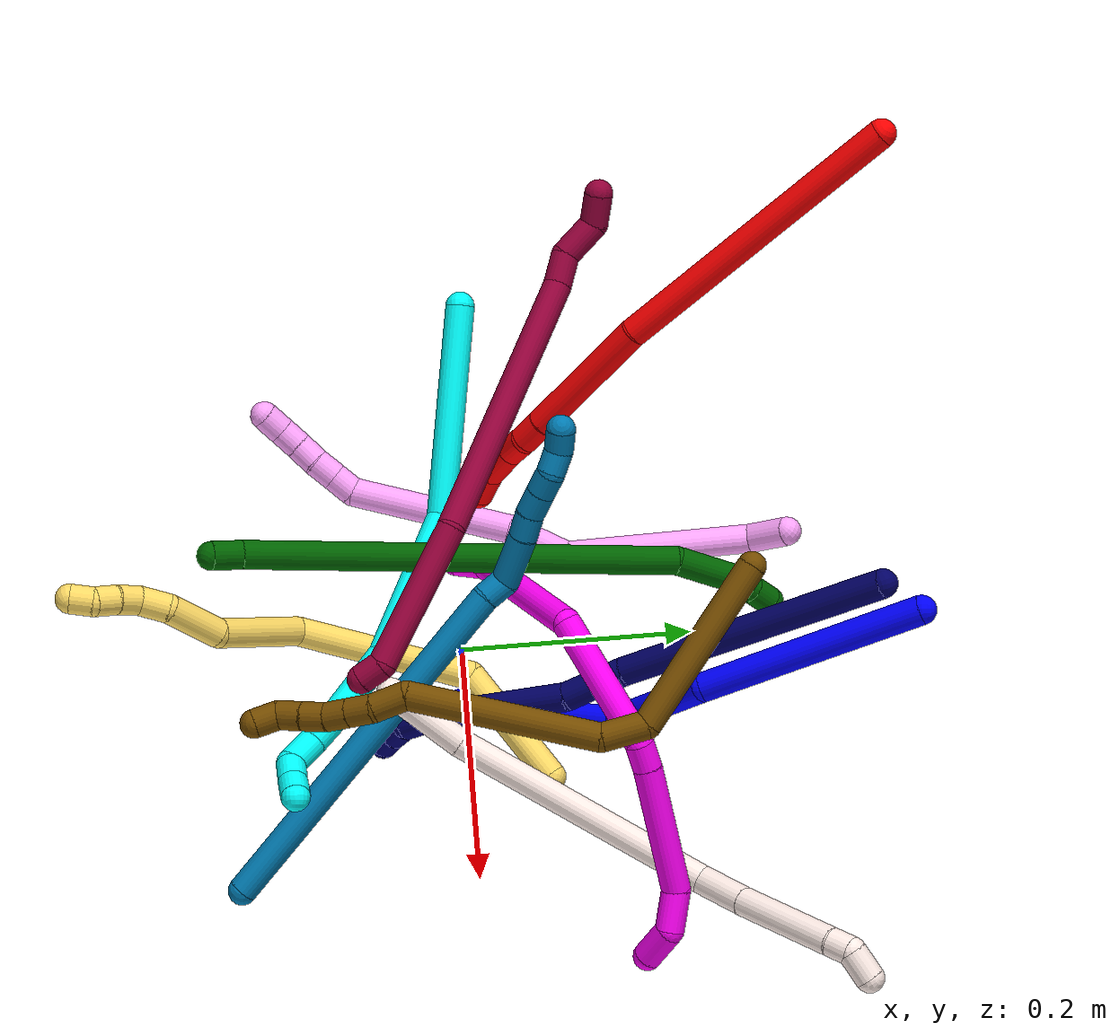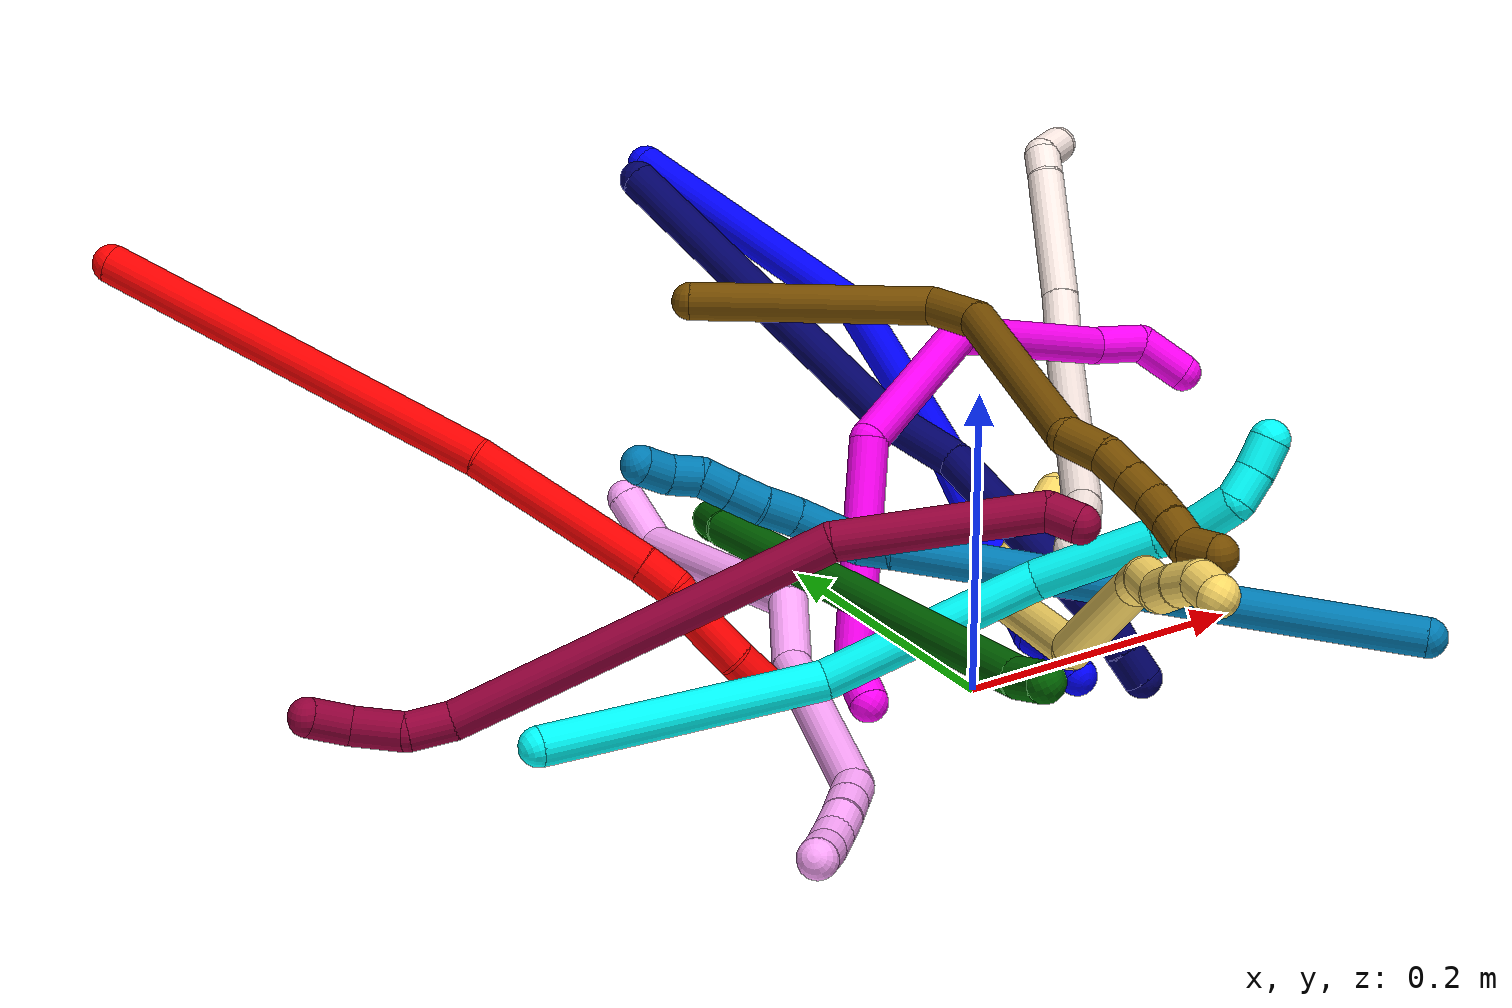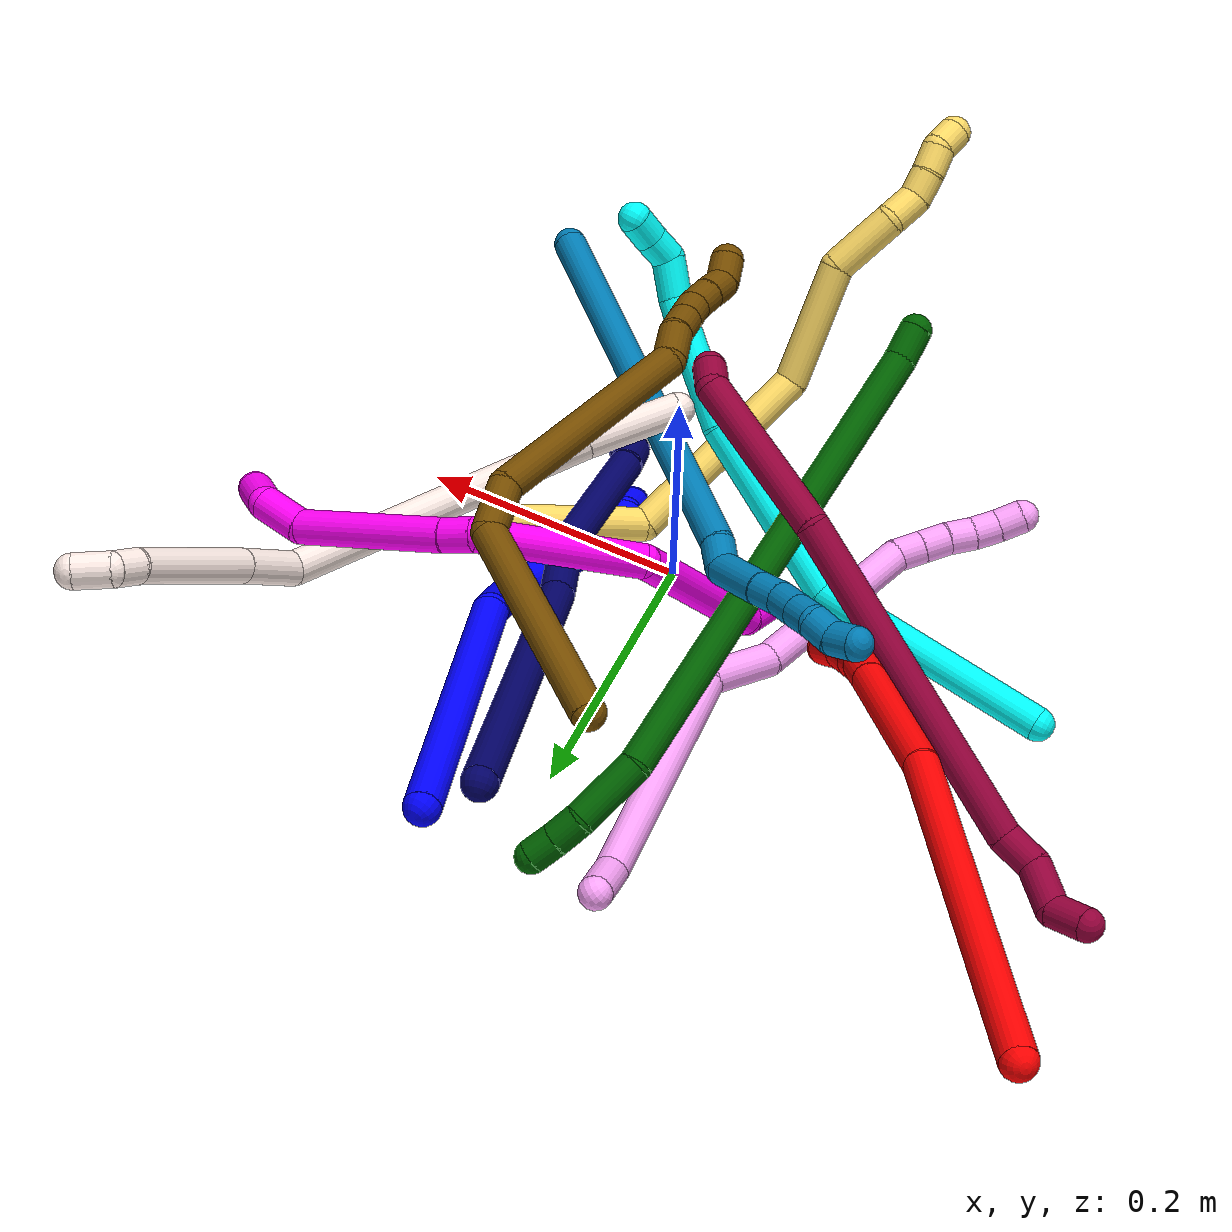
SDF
<sdf version="1.7">
 <world name="default">
  <plugin name="TubeGeneratorPlugin" filename="libtube_generator_plugin.so"/>
  <model name="photoneo_s_sensor">
   <static>1</static>
   <pose>0 0 2 1.57079 1.57079 3.14159</pose>
   <link name="link">
    <inertial><mass>0.1</mass></inertial>
    <sensor name="sensor" type="depth">
     <update_rate>30</update_rate>
     <camera>
      <horizontal_fov>1.22</horizontal_fov>
      <image><width>1920</width><height>1200</height><format>B8G8R8</format></image>
      <clip><near>0.1</near><far>4</far></clip>
      <depth_camera><output>points</output></depth_camera>
     </camera>
     <plugin name="camera_plugin" filename="libgazebo_ros_depth_camera.so">
      <baseline>0.2</baseline>
      <alwaysOn>1</alwaysOn>
      <updateRate>0.0</updateRate>
      <cameraName>camera_ir</cameraName>
      <imageTopicName>/camera/color/image_raw</imageTopicName>
      <cameraInfoTopicName>/camera/color/camera_info</cameraInfoTopicName>
      <depthImageTopicName>/camera/depth/image_raw</depthImageTopicName>
      <depthImageCameraInfoTopicName>/camera/depth/camera_info</depthImageCameraInfoTopicName>
      <pointCloudTopicName>/camera/depth/points</pointCloudTopicName>
      <frameName>fr_optical</frameName>
      <pointCloudCutoff>0.1</pointCloudCutoff>
      <pointCloudCutoffMax>2.0</pointCloudCutoffMax>
      <distortionK1>0</distortionK1>
      <distortionK2>0</distortionK2>
      <distortionK3>0</distortionK3>
      <distortionT1>0</distortionT1>
      <distortionT2>0</distortionT2>
      <CxPrime>0</CxPrime>
      <Cx>0</Cx>
      <Cy>0</Cy>
      <focalLength>0</focalLength>
      <hackBaseline>0</hackBaseline>
     </plugin>
    </sensor>
   </link>
  </model>
  <gravity>0 0 -9.8</gravity>
  <magnetic_field>6e-06 2.3e-05 -4.2e-05</magnetic_field>
  <atmosphere type="adiabatic"/>
  <physics name="default_physics" default="0" type="ode">
   <max_step_size>0.003</max_step_size>
   <real_time_factor>1</real_time_factor>
   <real_time_update_rate>1000</real_time_update_rate>
   <max_contacts>10000</max_contacts>
   <ode>
    <solver>
     <type>quick</type>
     <iters>100</iters>
     <sor>1.3</sor>
     <use_dynamic_moi_rescaling>0</use_dynamic_moi_rescaling>
    </solver>
    <constraints>
     <contact_max_correcting_vel>0</contact_max_correcting_vel>
     <contact_surface_layer>0.001</contact_surface_layer>
     <cfm>0</cfm>
     <erp>0.2</erp>
    </constraints>
   </ode>
  </physics>
  <scene><ambient>0.4 0.4 0.4 1</ambient><background>0.7 0.7 0.7 1</background><shadows>0</shadows></scene>
  <audio><device>default</device></audio>
  <spherical_coordinates>
   <surface_model>EARTH_WGS84</surface_model>
   <latitude_deg>0</latitude_deg>
   <longitude_deg>0</longitude_deg>
   <elevation>0</elevation>
   <heading_deg>0</heading_deg>
  </spherical_coordinates>
  <model name="bin">
   <static>1</static>
   <link name="bottom">
    <collision name="collision-bottom">
     <pose>0 0 -0.01 0 -0 0</pose>
     <geometry><box><size>0.8 0.6 0.02</size></box></geometry>
     <surface>
      <friction><ode><mu>100</mu><mu2>100</mu2></ode></friction>
      <contact><collide_bitmask>65535</collide_bitmask></contact>
     </surface>
    </collision>
   </link>
   <link name="west_wall">
    <collision name="collision-west_wall">
     <pose>-0.41 0 0.1 0 -0 0</pose>
     <geometry><box><size>0.02 0.6 0.2</size></box></geometry>
     <surface>
      <friction><ode><mu>100</mu><mu2>100</mu2></ode></friction>
      <contact><collide_bitmask>65535</collide_bitmask></contact>
     </surface>
    </collision>
   </link>
   <link name="east_wall">
    <collision name="collision-east_wall">
     <pose>0.41 0 0.1 0 -0 0</pose>
     <geometry><box><size>0.02 0.6 0.2</size></box></geometry>
     <surface>
      <friction><ode><mu>100</mu><mu2>100</mu2></ode></friction>
      <contact><collide_bitmask>65535</collide_bitmask></contact>
     </surface>
    </collision>
   </link>
   <link name="south_wall">
    <collision name="collision-south_wall">
     <pose>0 -0.31 0.1 0 -0 0</pose>
     <geometry><box><size>0.8 0.02 0.2</size></box></geometry>
     <surface>
      <friction><ode><mu>100</mu><mu2>100</mu2></ode></friction>
      <contact><collide_bitmask>65535</collide_bitmask></contact>
     </surface>
    </collision>
   </link>
   <link name="north_wall">
    <collision name="collision-north_wall">
     <pose>0 0.31 0.1 0 -0 0</pose>
     <geometry><box><size>0.8 0.02 0.2</size></box></geometry>
     <surface>
      <friction><ode><mu>100</mu><mu2>100</mu2></ode></friction>
      <contact><collide_bitmask>65535</collide_bitmask></contact>
     </surface>
    </collision>
   </link>
  </model>
  <model name="1">
   <static>0</static>
   <link name="1">
    <collision name="collision-cylinder-e_1_1_4">
     <pose>-0.028922 -0.023668 -0.090883 2.88683 -0.298747 -1.73142</pose>
     <geometry><cylinder><radius>0.0125</radius><length>0.196533</length></cylinder></geometry>
     <surface>
      <friction><ode><mu>1.16</mu><mu2>1.16</mu2><slip1>0</slip1><slip2>0</slip2></ode></friction>
      <contact><ode><kp>1e+06</kp><kd>1</kd><max_vel>0</max_vel><min_depth>0.001</min_depth></ode></contact>
     </surface>
    </collision>
    <visual name="visual-cylinder-e_1_1_4">
     <pose>-0.028922 -0.023668 -0.090883 2.88683 -0.298747 -1.73142</pose>
     <geometry><cylinder><radius>0.0125</radius><length>0.196533</length></cylinder></geometry>
     <material><ambient>0 0 1 1</ambient></material>
    </visual>
    <collision name="collision-cylinder-e_2_4_5">
     <pose>-0.069808 -0.088351 -0.220334 2.32544 -0.209386 -0.476834</pose>
     <geometry><cylinder><radius>0.0125</radius><length>0.115117</length></cylinder></geometry>
     <surface>
      <friction><ode><mu>1.16</mu><mu2>1.16</mu2><slip1>0</slip1><slip2>0</slip2></ode></friction>
      <contact><ode><kp>1e+06</kp><kd>1</kd><max_vel>0</max_vel><min_depth>0.001</min_depth></ode></contact>
     </surface>
    </collision>
    <visual name="visual-cylinder-e_2_4_5">
     <pose>-0.069808 -0.088351 -0.220334 2.32544 -0.209386 -0.476834</pose>
     <geometry><cylinder><radius>0.0125</radius><length>0.115117</length></cylinder></geometry>
     <material><ambient>0 0 1 1</ambient></material>
    </visual>
    <collision name="collision-cylinder-e_3_5_6">
     <pose>-0.076222 -0.147536 -0.297777 2.70442 0.128641 0.564431</pose>
     <geometry><cylinder><radius>0.0125</radius><length>0.086537</length></cylinder></geometry>
     <surface>
      <friction><ode><mu>1.16</mu><mu2>1.16</mu2><slip1>0</slip1><slip2>0</slip2></ode></friction>
      <contact><ode><kp>1e+06</kp><kd>1</kd><max_vel>0</max_vel><min_depth>0.001</min_depth></ode></contact>
     </surface>
    </collision>
    <visual name="visual-cylinder-e_3_5_6">
     <pose>-0.076222 -0.147536 -0.297777 2.70442 0.128641 0.564431</pose>
     <geometry><cylinder><radius>0.0125</radius><length>0.086537</length></cylinder></geometry>
     <material><ambient>0 0 1 1</ambient></material>
    </visual>
    <collision name="collision-cylinder-e_4_6_7">
     <pose>-0.069357 -0.170481 -0.346634 2.69522 0.118187 0.509976</pose>
     <geometry><cylinder><radius>0.0125</radius><length>0.022288</length></cylinder></geometry>
     <surface>
      <friction><ode><mu>1.16</mu><mu2>1.16</mu2><slip1>0</slip1><slip2>0</slip2></ode></friction>
      <contact><ode><kp>1e+06</kp><kd>1</kd><max_vel>0</max_vel><min_depth>0.001</min_depth></ode></contact>
     </surface>
    </collision>
    <visual name="visual-cylinder-e_4_6_7">
     <pose>-0.069357 -0.170481 -0.346634 2.69522 0.118187 0.509976</pose>
     <geometry><cylinder><radius>0.0125</radius><length>0.022288</length></cylinder></geometry>
     <material><ambient>0 0 1 1</ambient></material>
    </visual>
    <collision name="collision-cylinder-e_5_7_8">
     <pose>-0.064515 -0.180992 -0.374177 2.82598 0.18867 1.07285</pose>
     <geometry><cylinder><radius>0.0125</radius><length>0.037613</length></cylinder></geometry>
     <surface>
      <friction><ode><mu>1.16</mu><mu2>1.16</mu2><slip1>0</slip1><slip2>0</slip2></ode></friction>
      <contact><ode><kp>1e+06</kp><kd>1</kd><max_vel>0</max_vel><min_depth>0.001</min_depth></ode></contact>
     </surface>
    </collision>
    <visual name="visual-cylinder-e_5_7_8">
     <pose>-0.064515 -0.180992 -0.374177 2.82598 0.18867 1.07285</pose>
     <geometry><cylinder><radius>0.0125</radius><length>0.037613</length></cylinder></geometry>
     <material><ambient>0 0 1 1</ambient></material>
    </visual>
    <collision name="collision-cylinder-e_6_8_9">
     <pose>-0.063927 -0.18788 -0.401418 3.02299 -0.292756 -2.37594</pose>
     <geometry><cylinder><radius>0.0125</radius><length>0.020364</length></cylinder></geometry>
     <surface>
      <friction><ode><mu>1.16</mu><mu2>1.16</mu2><slip1>0</slip1><slip2>0</slip2></ode></friction>
      <contact><ode><kp>1e+06</kp><kd>1</kd><max_vel>0</max_vel><min_depth>0.001</min_depth></ode></contact>
     </surface>
    </collision>
    <visual name="visual-cylinder-e_6_8_9">
     <pose>-0.063927 -0.18788 -0.401418 3.02299 -0.292756 -2.37594</pose>
     <geometry><cylinder><radius>0.0125</radius><length>0.020364</length></cylinder></geometry>
     <material><ambient>0 0 1 1</ambient></material>
    </visual>
    <collision name="collision-cylinder-e_7_9_2">
     <pose>-0.068442 -0.194354 -0.420332 2.61888 -0.146914 -0.536968</pose>
     <geometry><cylinder><radius>0.0125</radius><length>0.021547</length></cylinder></geometry>
     <surface>
      <friction><ode><mu>1.16</mu><mu2>1.16</mu2><slip1>0</slip1><slip2>0</slip2></ode></friction>
      <contact><ode><kp>1e+06</kp><kd>1</kd><max_vel>0</max_vel><min_depth>0.001</min_depth></ode></contact>
     </surface>
    </collision>
    <visual name="visual-cylinder-e_7_9_2">
     <pose>-0.068442 -0.194354 -0.420332 2.61888 -0.146914 -0.536968</pose>
     <geometry><cylinder><radius>0.0125</radius><length>0.021547</length></cylinder></geometry>
     <material><ambient>0 0 1 1</ambient></material>
    </visual>
    <collision name="collision-sphere-2">
     <pose>-0.070019 -0.199674 -0.429567 0 -0 0</pose>
     <geometry><sphere><radius>0.0125</radius></sphere></geometry>
     <surface>
      <friction><ode><mu>1.16</mu><mu2>1.16</mu2><slip1>0</slip1><slip2>0</slip2></ode></friction>
      <contact><ode><kp>1e+06</kp><kd>1</kd><max_vel>0</max_vel><min_depth>0.001</min_depth></ode></contact>
     </surface>
    </collision>
    <visual name="visual-sphere-2">
     <pose>-0.070019 -0.199674 -0.429567 0 -0 0</pose>
     <geometry><sphere><radius>0.0125</radius></sphere></geometry>
     <material><ambient>0 0 1 1</ambient></material>
    </visual>
    <collision name="collision-sphere-9">
     <pose>-0.066865 -0.189033 -0.411098 0 -0 0</pose>
     <geometry><sphere><radius>0.0125</radius></sphere></geometry>
     <surface>
      <friction><ode><mu>1.16</mu><mu2>1.16</mu2><slip1>0</slip1><slip2>0</slip2></ode></friction>
      <contact><ode><kp>1e+06</kp><kd>1</kd><max_vel>0</max_vel><min_depth>0.001</min_depth></ode></contact>
     </surface>
    </collision>
    <visual name="visual-sphere-9">
     <pose>-0.066865 -0.189033 -0.411098 0 -0 0</pose>
     <geometry><sphere><radius>0.0125</radius></sphere></geometry>
     <material><ambient>0 0 1 1</ambient></material>
    </visual>
    <collision name="collision-sphere-4">
     <pose>-0.057844 -0.047335 -0.181765 0 -0 0</pose>
     <geometry><sphere><radius>0.0125</radius></sphere></geometry>
     <surface>
      <friction><ode><mu>1.16</mu><mu2>1.16</mu2><slip1>0</slip1><slip2>0</slip2></ode></friction>
      <contact><ode><kp>1e+06</kp><kd>1</kd><max_vel>0</max_vel><min_depth>0.001</min_depth></ode></contact>
     </surface>
    </collision>
    <visual name="visual-sphere-4">
     <pose>-0.057844 -0.047335 -0.181765 0 -0 0</pose>
     <geometry><sphere><radius>0.0125</radius></sphere></geometry>
     <material><ambient>0 0 1 1</ambient></material>
    </visual>
    <collision name="collision-sphere-1">
     <geometry><sphere><radius>0.0125</radius></sphere></geometry>
     <surface>
      <friction><ode><mu>1.16</mu><mu2>1.16</mu2><slip1>0</slip1><slip2>0</slip2></ode></friction>
      <contact><ode><kp>1e+06</kp><kd>1</kd><max_vel>0</max_vel><min_depth>0.001</min_depth></ode></contact>
     </surface>
    </collision>
    <visual name="visual-sphere-1">
     <geometry><sphere><radius>0.0125</radius></sphere></geometry>
     <material><ambient>0 0 1 1</ambient></material>
    </visual>
    <collision name="collision-sphere-8">
     <pose>-0.060988 -0.186726 -0.391737 0 -0 0</pose>
     <geometry><sphere><radius>0.0125</radius></sphere></geometry>
     <surface>
      <friction><ode><mu>1.16</mu><mu2>1.16</mu2><slip1>0</slip1><slip2>0</slip2></ode></friction>
      <contact><ode><kp>1e+06</kp><kd>1</kd><max_vel>0</max_vel><min_depth>0.001</min_depth></ode></contact>
     </surface>
    </collision>
    <visual name="visual-sphere-8">
     <pose>-0.060988 -0.186726 -0.391737 0 -0 0</pose>
     <geometry><sphere><radius>0.0125</radius></sphere></geometry>
     <material><ambient>0 0 1 1</ambient></material>
    </visual>
    <collision name="collision-sphere-5">
     <pose>-0.081772 -0.129368 -0.258902 0 -0 0</pose>
     <geometry><sphere><radius>0.0125</radius></sphere></geometry>
     <surface>
      <friction><ode><mu>1.16</mu><mu2>1.16</mu2><slip1>0</slip1><slip2>0</slip2></ode></friction>
      <contact><ode><kp>1e+06</kp><kd>1</kd><max_vel>0</max_vel><min_depth>0.001</min_depth></ode></contact>
     </surface>
    </collision>
    <visual name="visual-sphere-5">
     <pose>-0.081772 -0.129368 -0.258902 0 -0 0</pose>
     <geometry><sphere><radius>0.0125</radius></sphere></geometry>
     <material><ambient>0 0 1 1</ambient></material>
    </visual>
    <collision name="collision-sphere-6">
     <pose>-0.070671 -0.165703 -0.336652 0 -0 0</pose>
     <geometry><sphere><radius>0.0125</radius></sphere></geometry>
     <surface>
      <friction><ode><mu>1.16</mu><mu2>1.16</mu2><slip1>0</slip1><slip2>0</slip2></ode></friction>
      <contact><ode><kp>1e+06</kp><kd>1</kd><max_vel>0</max_vel><min_depth>0.001</min_depth></ode></contact>
     </surface>
    </collision>
    <visual name="visual-sphere-6">
     <pose>-0.070671 -0.165703 -0.336652 0 -0 0</pose>
     <geometry><sphere><radius>0.0125</radius></sphere></geometry>
     <material><ambient>0 0 1 1</ambient></material>
    </visual>
    <collision name="collision-sphere-7">
     <pose>-0.068043 -0.175258 -0.356616 0 -0 0</pose>
     <geometry><sphere><radius>0.0125</radius></sphere></geometry>
     <surface>
      <friction><ode><mu>1.16</mu><mu2>1.16</mu2><slip1>0</slip1><slip2>0</slip2></ode></friction>
      <contact><ode><kp>1e+06</kp><kd>1</kd><max_vel>0</max_vel><min_depth>0.001</min_depth></ode></contact>
     </surface>
    </collision>
    <visual name="visual-sphere-7">
     <pose>-0.068043 -0.175258 -0.356616 0 -0 0</pose>
     <geometry><sphere><radius>0.0125</radius></sphere></geometry>
     <material><ambient>0 0 1 1</ambient></material>
    </visual>
    <inertial>
     <pose>-0.054131 -0.092421 -0.216051 0 -0 0</pose>
     <mass>0.5</mass>
     <inertia>
      <ixx>-0.000565</ixx>
      <ixy>0</ixy>
      <ixz>0</ixz>
      <iyy>-0.000615</iyy>
      <iyz>0</iyz>
      <izz>0.00045</izz>
     </inertia>
    </inertial>
   </link>
   <pose>-0.007122 0.379865 0.236964 1.49733 0.066745 3.08041</pose>
  </model>
  <model name="2">
   <static>0</static>
   <link name="2">
    <collision name="collision-cylinder-e_1_1_4">
     <pose>0.040479 -0.037567 -0.122703 2.8445 0.30556 1.59931</pose>
     <geometry><cylinder><radius>0.0125</radius><length>0.269116</length></cylinder></geometry>
     <surface>
      <friction><ode><mu>1.16</mu><mu2>1.16</mu2><slip1>0</slip1><slip2>0</slip2></ode></friction>
      <contact><ode><kp>1e+06</kp><kd>1</kd><max_vel>0</max_vel><min_depth>0.001</min_depth></ode></contact>
     </surface>
    </collision>
    <visual name="visual-cylinder-e_1_1_4">
     <pose>0.040479 -0.037567 -0.122703 2.8445 0.30556 1.59931</pose>
     <geometry><cylinder><radius>0.0125</radius><length>0.269116</length></cylinder></geometry>
     <material><ambient>1 0 0 1</ambient></material>
    </visual>
    <collision name="collision-cylinder-e_2_4_5">
     <pose>0.092794 -0.083496 -0.303967 2.99975 0.19748 1.89731</pose>
     <geometry><cylinder><radius>0.0125</radius><length>0.120656</length></cylinder></geometry>
     <surface>
      <friction><ode><mu>1.16</mu><mu2>1.16</mu2><slip1>0</slip1><slip2>0</slip2></ode></friction>
      <contact><ode><kp>1e+06</kp><kd>1</kd><max_vel>0</max_vel><min_depth>0.001</min_depth></ode></contact>
     </surface>
    </collision>
    <visual name="visual-cylinder-e_2_4_5">
     <pose>0.092794 -0.083496 -0.303967 2.99975 0.19748 1.89731</pose>
     <geometry><cylinder><radius>0.0125</radius><length>0.120656</length></cylinder></geometry>
     <material><ambient>1 0 0 1</ambient></material>
    </visual>
    <collision name="collision-cylinder-e_3_5_6">
     <pose>0.106157 -0.093345 -0.374198 3.01496 0.129094 1.59006</pose>
     <geometry><cylinder><radius>0.0125</radius><length>0.023725</length></cylinder></geometry>
     <surface>
      <friction><ode><mu>1.16</mu><mu2>1.16</mu2><slip1>0</slip1><slip2>0</slip2></ode></friction>
      <contact><ode><kp>1e+06</kp><kd>1</kd><max_vel>0</max_vel><min_depth>0.001</min_depth></ode></contact>
     </surface>
    </collision>
    <visual name="visual-cylinder-e_3_5_6">
     <pose>0.106157 -0.093345 -0.374198 3.01496 0.129094 1.59006</pose>
     <geometry><cylinder><radius>0.0125</radius><length>0.023725</length></cylinder></geometry>
     <material><ambient>1 0 0 1</ambient></material>
    </visual>
    <collision name="collision-cylinder-e_4_6_7">
     <pose>0.105451 -0.095388 -0.397205 3.09247 -0.194299 -2.64771</pose>
     <geometry><cylinder><radius>0.0125</radius><length>0.023137</length></cylinder></geometry>
     <surface>
      <friction><ode><mu>1.16</mu><mu2>1.16</mu2><slip1>0</slip1><slip2>0</slip2></ode></friction>
      <contact><ode><kp>1e+06</kp><kd>1</kd><max_vel>0</max_vel><min_depth>0.001</min_depth></ode></contact>
     </surface>
    </collision>
    <visual name="visual-cylinder-e_4_6_7">
     <pose>0.105451 -0.095388 -0.397205 3.09247 -0.194299 -2.64771</pose>
     <geometry><cylinder><radius>0.0125</radius><length>0.023137</length></cylinder></geometry>
     <material><ambient>1 0 0 1</ambient></material>
    </visual>
    <collision name="collision-cylinder-e_5_7_8">
     <pose>0.102275 -0.096316 -0.425714 3.12003 -0.054777 -2.39176</pose>
     <geometry><cylinder><radius>0.0125</radius><length>0.034403</length></cylinder></geometry>
     <surface>
      <friction><ode><mu>1.16</mu><mu2>1.16</mu2><slip1>0</slip1><slip2>0</slip2></ode></friction>
      <contact><ode><kp>1e+06</kp><kd>1</kd><max_vel>0</max_vel><min_depth>0.001</min_depth></ode></contact>
     </surface>
    </collision>
    <visual name="visual-cylinder-e_5_7_8">
     <pose>0.102275 -0.096316 -0.425714 3.12003 -0.054777 -2.39176</pose>
     <geometry><cylinder><radius>0.0125</radius><length>0.034403</length></cylinder></geometry>
     <material><ambient>1 0 0 1</ambient></material>
    </visual>
    <collision name="collision-cylinder-e_6_8_2">
     <pose>0.101026 -0.09409 -0.457129 -2.96133 -0.021259 0.234158</pose>
     <geometry><cylinder><radius>0.0125</radius><length>0.028963</length></cylinder></geometry>
     <surface>
      <friction><ode><mu>1.16</mu><mu2>1.16</mu2><slip1>0</slip1><slip2>0</slip2></ode></friction>
      <contact><ode><kp>1e+06</kp><kd>1</kd><max_vel>0</max_vel><min_depth>0.001</min_depth></ode></contact>
     </surface>
    </collision>
    <visual name="visual-cylinder-e_6_8_2">
     <pose>0.101026 -0.09409 -0.457129 -2.96133 -0.021259 0.234158</pose>
     <geometry><cylinder><radius>0.0125</radius><length>0.028963</length></cylinder></geometry>
     <material><ambient>1 0 0 1</ambient></material>
    </visual>
    <collision name="collision-sphere-2">
     <pose>0.100718 -0.091494 -0.471373 0 -0 0</pose>
     <geometry><sphere><radius>0.0125</radius></sphere></geometry>
     <surface>
      <friction><ode><mu>1.16</mu><mu2>1.16</mu2><slip1>0</slip1><slip2>0</slip2></ode></friction>
      <contact><ode><kp>1e+06</kp><kd>1</kd><max_vel>0</max_vel><min_depth>0.001</min_depth></ode></contact>
     </surface>
    </collision>
    <visual name="visual-sphere-2">
     <pose>0.100718 -0.091494 -0.471373 0 -0 0</pose>
     <geometry><sphere><radius>0.0125</radius></sphere></geometry>
     <material><ambient>1 0 0 1</ambient></material>
    </visual>
    <collision name="collision-sphere-4">
     <pose>0.080957 -0.075133 -0.245406 0 -0 0</pose>
     <geometry><sphere><radius>0.0125</radius></sphere></geometry>
     <surface>
      <friction><ode><mu>1.16</mu><mu2>1.16</mu2><slip1>0</slip1><slip2>0</slip2></ode></friction>
      <contact><ode><kp>1e+06</kp><kd>1</kd><max_vel>0</max_vel><min_depth>0.001</min_depth></ode></contact>
     </surface>
    </collision>
    <visual name="visual-sphere-4">
     <pose>0.080957 -0.075133 -0.245406 0 -0 0</pose>
     <geometry><sphere><radius>0.0125</radius></sphere></geometry>
     <material><ambient>1 0 0 1</ambient></material>
    </visual>
    <collision name="collision-sphere-1">
     <geometry><sphere><radius>0.0125</radius></sphere></geometry>
     <surface>
      <friction><ode><mu>1.16</mu><mu2>1.16</mu2><slip1>0</slip1><slip2>0</slip2></ode></friction>
      <contact><ode><kp>1e+06</kp><kd>1</kd><max_vel>0</max_vel><min_depth>0.001</min_depth></ode></contact>
     </surface>
    </collision>
    <visual name="visual-sphere-1">
     <geometry><sphere><radius>0.0125</radius></sphere></geometry>
     <material><ambient>1 0 0 1</ambient></material>
    </visual>
    <collision name="collision-sphere-8">
     <pose>0.101333 -0.096686 -0.442886 0 -0 0</pose>
     <geometry><sphere><radius>0.0125</radius></sphere></geometry>
     <surface>
      <friction><ode><mu>1.16</mu><mu2>1.16</mu2><slip1>0</slip1><slip2>0</slip2></ode></friction>
      <contact><ode><kp>1e+06</kp><kd>1</kd><max_vel>0</max_vel><min_depth>0.001</min_depth></ode></contact>
     </surface>
    </collision>
    <visual name="visual-sphere-8">
     <pose>0.101333 -0.096686 -0.442886 0 -0 0</pose>
     <geometry><sphere><radius>0.0125</radius></sphere></geometry>
     <material><ambient>1 0 0 1</ambient></material>
    </visual>
    <collision name="collision-sphere-5">
     <pose>0.10463 -0.091859 -0.362529 0 -0 0</pose>
     <geometry><sphere><radius>0.0125</radius></sphere></geometry>
     <surface>
      <friction><ode><mu>1.16</mu><mu2>1.16</mu2><slip1>0</slip1><slip2>0</slip2></ode></friction>
      <contact><ode><kp>1e+06</kp><kd>1</kd><max_vel>0</max_vel><min_depth>0.001</min_depth></ode></contact>
     </surface>
    </collision>
    <visual name="visual-sphere-5">
     <pose>0.10463 -0.091859 -0.362529 0 -0 0</pose>
     <geometry><sphere><radius>0.0125</radius></sphere></geometry>
     <material><ambient>1 0 0 1</ambient></material>
    </visual>
    <collision name="collision-sphere-6">
     <pose>0.107684 -0.09483 -0.385868 0 -0 0</pose>
     <geometry><sphere><radius>0.0125</radius></sphere></geometry>
     <surface>
      <friction><ode><mu>1.16</mu><mu2>1.16</mu2><slip1>0</slip1><slip2>0</slip2></ode></friction>
      <contact><ode><kp>1e+06</kp><kd>1</kd><max_vel>0</max_vel><min_depth>0.001</min_depth></ode></contact>
     </surface>
    </collision>
    <visual name="visual-sphere-6">
     <pose>0.107684 -0.09483 -0.385868 0 -0 0</pose>
     <geometry><sphere><radius>0.0125</radius></sphere></geometry>
     <material><ambient>1 0 0 1</ambient></material>
    </visual>
    <collision name="collision-sphere-7">
     <pose>0.103217 -0.095945 -0.408542 0 -0 0</pose>
     <geometry><sphere><radius>0.0125</radius></sphere></geometry>
     <surface>
      <friction><ode><mu>1.16</mu><mu2>1.16</mu2><slip1>0</slip1><slip2>0</slip2></ode></friction>
      <contact><ode><kp>1e+06</kp><kd>1</kd><max_vel>0</max_vel><min_depth>0.001</min_depth></ode></contact>
     </surface>
    </collision>
    <visual name="visual-sphere-7">
     <pose>0.103217 -0.095945 -0.408542 0 -0 0</pose>
     <geometry><sphere><radius>0.0125</radius></sphere></geometry>
     <material><ambient>1 0 0 1</ambient></material>
    </visual>
    <inertial>
     <pose>0.066985 -0.061289 -0.231301 0 -0 0</pose>
     <mass>0.5</mass>
     <inertia>
      <ixx>0.001611</ixx>
      <ixy>0</ixy>
      <ixz>0</ixz>
      <iyy>0.001933</iyy>
      <iyz>0</iyz>
      <izz>-8.1e-05</izz>
     </inertia>
    </inertial>
   </link>
   <pose>-0.397385 0.3776 0.244294 -0.348209 -0.789284 -0.330621</pose>
  </model>
  <model name="3">
   <static>0</static>
   <link name="3">
    <collision name="collision-cylinder-e_1_1_4">
     <pose>0.011995 0.010157 0.090344 -0.111955 0.131186 -0.007362</pose>
     <geometry><cylinder><radius>0.0125</radius><length>0.183403</length></cylinder></geometry>
     <surface>
      <friction><ode><mu>1.16</mu><mu2>1.16</mu2><slip1>0</slip1><slip2>0</slip2></ode></friction>
      <contact><ode><kp>1e+06</kp><kd>1</kd><max_vel>0</max_vel><min_depth>0.001</min_depth></ode></contact>
     </surface>
    </collision>
    <visual name="visual-cylinder-e_1_1_4">
     <pose>0.011995 0.010157 0.090344 -0.111955 0.131186 -0.007362</pose>
     <geometry><cylinder><radius>0.0125</radius><length>0.183403</length></cylinder></geometry>
     <material><ambient>0.003922 1 0.996078 1</ambient></material>
    </visual>
    <collision name="collision-cylinder-e_2_4_5">
     <pose>0.051692 -0.000847 0.24241 0.330285 0.401487 0.067799</pose>
     <geometry><cylinder><radius>0.0125</radius><length>0.141771</length></cylinder></geometry>
     <surface>
      <friction><ode><mu>1.16</mu><mu2>1.16</mu2><slip1>0</slip1><slip2>0</slip2></ode></friction>
      <contact><ode><kp>1e+06</kp><kd>1</kd><max_vel>0</max_vel><min_depth>0.001</min_depth></ode></contact>
     </surface>
    </collision>
    <visual name="visual-cylinder-e_2_4_5">
     <pose>0.051692 -0.000847 0.24241 0.330285 0.401487 0.067799</pose>
     <geometry><cylinder><radius>0.0125</radius><length>0.141771</length></cylinder></geometry>
     <material><ambient>0.003922 1 0.996078 1</ambient></material>
    </visual>
    <collision name="collision-cylinder-e_3_5_6">
     <pose>0.102412 -0.033984 0.333163 0.391268 0.63253 0.12952</pose>
     <geometry><cylinder><radius>0.0125</radius><length>0.077874</length></cylinder></geometry>
     <surface>
      <friction><ode><mu>1.16</mu><mu2>1.16</mu2><slip1>0</slip1><slip2>0</slip2></ode></friction>
      <contact><ode><kp>1e+06</kp><kd>1</kd><max_vel>0</max_vel><min_depth>0.001</min_depth></ode></contact>
     </surface>
    </collision>
    <visual name="visual-cylinder-e_3_5_6">
     <pose>0.102412 -0.033984 0.333163 0.391268 0.63253 0.12952</pose>
     <geometry><cylinder><radius>0.0125</radius><length>0.077874</length></cylinder></geometry>
     <material><ambient>0.003922 1 0.996078 1</ambient></material>
    </visual>
    <collision name="collision-cylinder-e_4_6_7">
     <pose>0.133197 -0.048636 0.370637 0.306805 0.719841 0.116238</pose>
     <geometry><cylinder><radius>0.0125</radius><length>0.02356</length></cylinder></geometry>
     <surface>
      <friction><ode><mu>1.16</mu><mu2>1.16</mu2><slip1>0</slip1><slip2>0</slip2></ode></friction>
      <contact><ode><kp>1e+06</kp><kd>1</kd><max_vel>0</max_vel><min_depth>0.001</min_depth></ode></contact>
     </surface>
    </collision>
    <visual name="visual-cylinder-e_4_6_7">
     <pose>0.133197 -0.048636 0.370637 0.306805 0.719841 0.116238</pose>
     <geometry><cylinder><radius>0.0125</radius><length>0.02356</length></cylinder></geometry>
     <material><ambient>0.003922 1 0.996078 1</ambient></material>
    </visual>
    <collision name="collision-cylinder-e_5_7_8">
     <pose>0.149979 -0.0601 0.388593 0.745919 0.608142 0.244341</pose>
     <geometry><cylinder><radius>0.0125</radius><length>0.031561</length></cylinder></geometry>
     <surface>
      <friction><ode><mu>1.16</mu><mu2>1.16</mu2><slip1>0</slip1><slip2>0</slip2></ode></friction>
      <contact><ode><kp>1e+06</kp><kd>1</kd><max_vel>0</max_vel><min_depth>0.001</min_depth></ode></contact>
     </surface>
    </collision>
    <visual name="visual-cylinder-e_5_7_8">
     <pose>0.149979 -0.0601 0.388593 0.745919 0.608142 0.244341</pose>
     <geometry><cylinder><radius>0.0125</radius><length>0.031561</length></cylinder></geometry>
     <material><ambient>0.003922 1 0.996078 1</ambient></material>
    </visual>
    <collision name="collision-cylinder-e_6_8_9">
     <pose>0.158289 -0.075552 0.406345 0.679995 -0.066593 -0.023564</pose>
     <geometry><cylinder><radius>0.0125</radius><length>0.02124</length></cylinder></geometry>
     <surface>
      <friction><ode><mu>1.16</mu><mu2>1.16</mu2><slip1>0</slip1><slip2>0</slip2></ode></friction>
      <contact><ode><kp>1e+06</kp><kd>1</kd><max_vel>0</max_vel><min_depth>0.001</min_depth></ode></contact>
     </surface>
    </collision>
    <visual name="visual-cylinder-e_6_8_9">
     <pose>0.158289 -0.075552 0.406345 0.679995 -0.066593 -0.023564</pose>
     <geometry><cylinder><radius>0.0125</radius><length>0.02124</length></cylinder></geometry>
     <material><ambient>0.003922 1 0.996078 1</ambient></material>
    </visual>
    <collision name="collision-cylinder-e_7_9_2">
     <pose>0.156534 -0.089636 0.421645 0.810312 -0.101932 -0.043748</pose>
     <geometry><cylinder><radius>0.0125</radius><length>0.020592</length></cylinder></geometry>
     <surface>
      <friction><ode><mu>1.16</mu><mu2>1.16</mu2><slip1>0</slip1><slip2>0</slip2></ode></friction>
      <contact><ode><kp>1e+06</kp><kd>1</kd><max_vel>0</max_vel><min_depth>0.001</min_depth></ode></contact>
     </surface>
    </collision>
    <visual name="visual-cylinder-e_7_9_2">
     <pose>0.156534 -0.089636 0.421645 0.810312 -0.101932 -0.043748</pose>
     <geometry><cylinder><radius>0.0125</radius><length>0.020592</length></cylinder></geometry>
     <material><ambient>0.003922 1 0.996078 1</ambient></material>
    </visual>
    <collision name="collision-sphere-2">
     <pose>0.155487 -0.097057 0.428705 0 -0 0</pose>
     <geometry><sphere><radius>0.0125</radius></sphere></geometry>
     <surface>
      <friction><ode><mu>1.16</mu><mu2>1.16</mu2><slip1>0</slip1><slip2>0</slip2></ode></friction>
      <contact><ode><kp>1e+06</kp><kd>1</kd><max_vel>0</max_vel><min_depth>0.001</min_depth></ode></contact>
     </surface>
    </collision>
    <visual name="visual-sphere-2">
     <pose>0.155487 -0.097057 0.428705 0 -0 0</pose>
     <geometry><sphere><radius>0.0125</radius></sphere></geometry>
     <material><ambient>0.003922 1 0.996078 1</ambient></material>
    </visual>
    <collision name="collision-sphere-9">
     <pose>0.157582 -0.082215 0.414585 0 -0 0</pose>
     <geometry><sphere><radius>0.0125</radius></sphere></geometry>
     <surface>
      <friction><ode><mu>1.16</mu><mu2>1.16</mu2><slip1>0</slip1><slip2>0</slip2></ode></friction>
      <contact><ode><kp>1e+06</kp><kd>1</kd><max_vel>0</max_vel><min_depth>0.001</min_depth></ode></contact>
     </surface>
    </collision>
    <visual name="visual-sphere-9">
     <pose>0.157582 -0.082215 0.414585 0 -0 0</pose>
     <geometry><sphere><radius>0.0125</radius></sphere></geometry>
     <material><ambient>0.003922 1 0.996078 1</ambient></material>
    </visual>
    <collision name="collision-sphere-4">
     <pose>0.023991 0.020314 0.180688 0 -0 0</pose>
     <geometry><sphere><radius>0.0125</radius></sphere></geometry>
     <surface>
      <friction><ode><mu>1.16</mu><mu2>1.16</mu2><slip1>0</slip1><slip2>0</slip2></ode></friction>
      <contact><ode><kp>1e+06</kp><kd>1</kd><max_vel>0</max_vel><min_depth>0.001</min_depth></ode></contact>
     </surface>
    </collision>
    <visual name="visual-sphere-4">
     <pose>0.023991 0.020314 0.180688 0 -0 0</pose>
     <geometry><sphere><radius>0.0125</radius></sphere></geometry>
     <material><ambient>0.003922 1 0.996078 1</ambient></material>
    </visual>
    <collision name="collision-sphere-1">
     <geometry><sphere><radius>0.0125</radius></sphere></geometry>
     <surface>
      <friction><ode><mu>1.16</mu><mu2>1.16</mu2><slip1>0</slip1><slip2>0</slip2></ode></friction>
      <contact><ode><kp>1e+06</kp><kd>1</kd><max_vel>0</max_vel><min_depth>0.001</min_depth></ode></contact>
     </surface>
    </collision>
    <visual name="visual-sphere-1">
     <geometry><sphere><radius>0.0125</radius></sphere></geometry>
     <material><ambient>0.003922 1 0.996078 1</ambient></material>
    </visual>
    <collision name="collision-sphere-8">
     <pose>0.158995 -0.068889 0.398106 0 -0 0</pose>
     <geometry><sphere><radius>0.0125</radius></sphere></geometry>
     <surface>
      <friction><ode><mu>1.16</mu><mu2>1.16</mu2><slip1>0</slip1><slip2>0</slip2></ode></friction>
      <contact><ode><kp>1e+06</kp><kd>1</kd><max_vel>0</max_vel><min_depth>0.001</min_depth></ode></contact>
     </surface>
    </collision>
    <visual name="visual-sphere-8">
     <pose>0.158995 -0.068889 0.398106 0 -0 0</pose>
     <geometry><sphere><radius>0.0125</radius></sphere></geometry>
     <material><ambient>0.003922 1 0.996078 1</ambient></material>
    </visual>
    <collision name="collision-sphere-5">
     <pose>0.079393 -0.022008 0.304132 0 -0 0</pose>
     <geometry><sphere><radius>0.0125</radius></sphere></geometry>
     <surface>
      <friction><ode><mu>1.16</mu><mu2>1.16</mu2><slip1>0</slip1><slip2>0</slip2></ode></friction>
      <contact><ode><kp>1e+06</kp><kd>1</kd><max_vel>0</max_vel><min_depth>0.001</min_depth></ode></contact>
     </surface>
    </collision>
    <visual name="visual-sphere-5">
     <pose>0.079393 -0.022008 0.304132 0 -0 0</pose>
     <geometry><sphere><radius>0.0125</radius></sphere></geometry>
     <material><ambient>0.003922 1 0.996078 1</ambient></material>
    </visual>
    <collision name="collision-sphere-6">
     <pose>0.125431 -0.045961 0.362194 0 -0 0</pose>
     <geometry><sphere><radius>0.0125</radius></sphere></geometry>
     <surface>
      <friction><ode><mu>1.16</mu><mu2>1.16</mu2><slip1>0</slip1><slip2>0</slip2></ode></friction>
      <contact><ode><kp>1e+06</kp><kd>1</kd><max_vel>0</max_vel><min_depth>0.001</min_depth></ode></contact>
     </surface>
    </collision>
    <visual name="visual-sphere-6">
     <pose>0.125431 -0.045961 0.362194 0 -0 0</pose>
     <geometry><sphere><radius>0.0125</radius></sphere></geometry>
     <material><ambient>0.003922 1 0.996078 1</ambient></material>
    </visual>
    <collision name="collision-sphere-7">
     <pose>0.140963 -0.051311 0.379081 0 -0 0</pose>
     <geometry><sphere><radius>0.0125</radius></sphere></geometry>
     <surface>
      <friction><ode><mu>1.16</mu><mu2>1.16</mu2><slip1>0</slip1><slip2>0</slip2></ode></friction>
      <contact><ode><kp>1e+06</kp><kd>1</kd><max_vel>0</max_vel><min_depth>0.001</min_depth></ode></contact>
     </surface>
    </collision>
    <visual name="visual-sphere-7">
     <pose>0.140963 -0.051311 0.379081 0 -0 0</pose>
     <geometry><sphere><radius>0.0125</radius></sphere></geometry>
     <material><ambient>0.003922 1 0.996078 1</ambient></material>
    </visual>
    <inertial>
     <pose>0.063921 -0.014794 0.230381 0 -0 0</pose>
     <mass>0.5</mass>
     <inertia>
      <ixx>0.00081</ixx>
      <ixy>0</ixy>
      <ixz>0</ixz>
      <iyy>0.000806</iyy>
      <iyz>0</iyz>
      <izz>-0.000125</izz>
     </inertia>
    </inertial>
   </link>
   <pose>-0.297037 0.022958 0.034062 -1.41952 -0.022528 -1.60954</pose>
  </model>
  <model name="4">
   <static>0</static>
   <link name="4">
    <collision name="collision-cylinder-e_1_1_4">
     <pose>-0.009699 -0.016584 -0.001418 1.6561 -0.527582 -0.572189</pose>
     <geometry><cylinder><radius>0.0125</radius><length>0.038529</length></cylinder></geometry>
     <surface>
      <friction><ode><mu>1.16</mu><mu2>1.16</mu2><slip1>0</slip1><slip2>0</slip2></ode></friction>
      <contact><ode><kp>1e+06</kp><kd>1</kd><max_vel>0</max_vel><min_depth>0.001</min_depth></ode></contact>
     </surface>
    </collision>
    <visual name="visual-cylinder-e_1_1_4">
     <pose>-0.009699 -0.016584 -0.001418 1.6561 -0.527582 -0.572189</pose>
     <geometry><cylinder><radius>0.0125</radius><length>0.038529</length></cylinder></geometry>
     <material><ambient>1 0.65098 0.996078 1</ambient></material>
    </visual>
    <collision name="collision-cylinder-e_2_4_5">
     <pose>-0.072358 -0.065698 -0.054284 2.57777 -0.716039 -1.82411</pose>
     <geometry><cylinder><radius>0.0125</radius><length>0.161368</length></cylinder></geometry>
     <surface>
      <friction><ode><mu>1.16</mu><mu2>1.16</mu2><slip1>0</slip1><slip2>0</slip2></ode></friction>
      <contact><ode><kp>1e+06</kp><kd>1</kd><max_vel>0</max_vel><min_depth>0.001</min_depth></ode></contact>
     </surface>
    </collision>
    <visual name="visual-cylinder-e_2_4_5">
     <pose>-0.072358 -0.065698 -0.054284 2.57777 -0.716039 -1.82411</pose>
     <geometry><cylinder><radius>0.0125</radius><length>0.161368</length></cylinder></geometry>
     <material><ambient>1 0.65098 0.996078 1</ambient></material>
    </visual>
    <collision name="collision-cylinder-e_3_5_6">
     <pose>-0.128258 -0.122017 -0.120862 2.13729 -0.103875 -0.188781</pose>
     <geometry><cylinder><radius>0.0125</radius><length>0.056692</length></cylinder></geometry>
     <surface>
      <friction><ode><mu>1.16</mu><mu2>1.16</mu2><slip1>0</slip1><slip2>0</slip2></ode></friction>
      <contact><ode><kp>1e+06</kp><kd>1</kd><max_vel>0</max_vel><min_depth>0.001</min_depth></ode></contact>
     </surface>
    </collision>
    <visual name="visual-cylinder-e_3_5_6">
     <pose>-0.128258 -0.122017 -0.120862 2.13729 -0.103875 -0.188781</pose>
     <geometry><cylinder><radius>0.0125</radius><length>0.056692</length></cylinder></geometry>
     <material><ambient>1 0.65098 0.996078 1</ambient></material>
    </visual>
    <collision name="collision-cylinder-e_4_6_7">
     <pose>-0.156318 -0.191676 -0.183775 2.37661 -0.362501 -0.854887</pose>
     <geometry><cylinder><radius>0.0125</radius><length>0.141679</length></cylinder></geometry>
     <surface>
      <friction><ode><mu>1.16</mu><mu2>1.16</mu2><slip1>0</slip1><slip2>0</slip2></ode></friction>
      <contact><ode><kp>1e+06</kp><kd>1</kd><max_vel>0</max_vel><min_depth>0.001</min_depth></ode></contact>
     </surface>
    </collision>
    <visual name="visual-cylinder-e_4_6_7">
     <pose>-0.156318 -0.191676 -0.183775 2.37661 -0.362501 -0.854887</pose>
     <geometry><cylinder><radius>0.0125</radius><length>0.141679</length></cylinder></geometry>
     <material><ambient>1 0.65098 0.996078 1</ambient></material>
    </visual>
    <collision name="collision-cylinder-e_5_7_8">
     <pose>-0.180814 -0.243049 -0.240299 2.57969 0.060431 0.208708</pose>
     <geometry><cylinder><radius>0.0125</radius><length>0.020698</length></cylinder></geometry>
     <surface>
      <friction><ode><mu>1.16</mu><mu2>1.16</mu2><slip1>0</slip1><slip2>0</slip2></ode></friction>
      <contact><ode><kp>1e+06</kp><kd>1</kd><max_vel>0</max_vel><min_depth>0.001</min_depth></ode></contact>
     </surface>
    </collision>
    <visual name="visual-cylinder-e_5_7_8">
     <pose>-0.180814 -0.243049 -0.240299 2.57969 0.060431 0.208708</pose>
     <geometry><cylinder><radius>0.0125</radius><length>0.020698</length></cylinder></geometry>
     <material><ambient>1 0.65098 0.996078 1</ambient></material>
    </visual>
    <collision name="collision-cylinder-e_6_8_9">
     <pose>-0.179653 -0.254057 -0.25771 2.57589 0.052108 0.178847</pose>
     <geometry><cylinder><radius>0.0125</radius><length>0.020566</length></cylinder></geometry>
     <surface>
      <friction><ode><mu>1.16</mu><mu2>1.16</mu2><slip1>0</slip1><slip2>0</slip2></ode></friction>
      <contact><ode><kp>1e+06</kp><kd>1</kd><max_vel>0</max_vel><min_depth>0.001</min_depth></ode></contact>
     </surface>
    </collision>
    <visual name="visual-cylinder-e_6_8_9">
     <pose>-0.179653 -0.254057 -0.25771 2.57589 0.052108 0.178847</pose>
     <geometry><cylinder><radius>0.0125</radius><length>0.020566</length></cylinder></geometry>
     <material><ambient>1 0.65098 0.996078 1</ambient></material>
    </visual>
    <collision name="collision-cylinder-e_7_9_10">
     <pose>-0.177576 -0.265763 -0.274329 2.47913 0.151674 0.434897</pose>
     <geometry><cylinder><radius>0.0125</radius><length>0.0204</length></cylinder></geometry>
     <surface>
      <friction><ode><mu>1.16</mu><mu2>1.16</mu2><slip1>0</slip1><slip2>0</slip2></ode></friction>
      <contact><ode><kp>1e+06</kp><kd>1</kd><max_vel>0</max_vel><min_depth>0.001</min_depth></ode></contact>
     </surface>
    </collision>
    <visual name="visual-cylinder-e_7_9_10">
     <pose>-0.177576 -0.265763 -0.274329 2.47913 0.151674 0.434897</pose>
     <geometry><cylinder><radius>0.0125</radius><length>0.0204</length></cylinder></geometry>
     <material><ambient>1 0.65098 0.996078 1</ambient></material>
    </visual>
    <collision name="collision-cylinder-e_8_10_11">
     <pose>-0.175054 -0.27699 -0.290902 2.61392 0.097965 0.35904</pose>
     <geometry><cylinder><radius>0.0125</radius><length>0.020056</length></cylinder></geometry>
     <surface>
      <friction><ode><mu>1.16</mu><mu2>1.16</mu2><slip1>0</slip1><slip2>0</slip2></ode></friction>
      <contact><ode><kp>1e+06</kp><kd>1</kd><max_vel>0</max_vel><min_depth>0.001</min_depth></ode></contact>
     </surface>
    </collision>
    <visual name="visual-cylinder-e_8_10_11">
     <pose>-0.175054 -0.27699 -0.290902 2.61392 0.097965 0.35904</pose>
     <geometry><cylinder><radius>0.0125</radius><length>0.020056</length></cylinder></geometry>
     <material><ambient>1 0.65098 0.996078 1</ambient></material>
    </visual>
    <collision name="collision-cylinder-e_9_11_2">
     <pose>-0.173317 -0.285724 -0.308787 2.76078 0.075722 0.388117</pose>
     <geometry><cylinder><radius>0.0125</radius><length>0.020013</length></cylinder></geometry>
     <surface>
      <friction><ode><mu>1.16</mu><mu2>1.16</mu2><slip1>0</slip1><slip2>0</slip2></ode></friction>
      <contact><ode><kp>1e+06</kp><kd>1</kd><max_vel>0</max_vel><min_depth>0.001</min_depth></ode></contact>
     </surface>
    </collision>
    <visual name="visual-cylinder-e_9_11_2">
     <pose>-0.173317 -0.285724 -0.308787 2.76078 0.075722 0.388117</pose>
     <geometry><cylinder><radius>0.0125</radius><length>0.020013</length></cylinder></geometry>
     <material><ambient>1 0.65098 0.996078 1</ambient></material>
    </visual>
    <collision name="collision-sphere-2">
     <pose>-0.17256 -0.289432 -0.31805 0 -0 0</pose>
     <geometry><sphere><radius>0.0125</radius></sphere></geometry>
     <surface>
      <friction><ode><mu>1.16</mu><mu2>1.16</mu2><slip1>0</slip1><slip2>0</slip2></ode></friction>
      <contact><ode><kp>1e+06</kp><kd>1</kd><max_vel>0</max_vel><min_depth>0.001</min_depth></ode></contact>
     </surface>
    </collision>
    <visual name="visual-sphere-2">
     <pose>-0.17256 -0.289432 -0.31805 0 -0 0</pose>
     <geometry><sphere><radius>0.0125</radius></sphere></geometry>
     <material><ambient>1 0.65098 0.996078 1</ambient></material>
    </visual>
    <collision name="collision-sphere-11">
     <pose>-0.174074 -0.282015 -0.299524 0 -0 0</pose>
     <geometry><sphere><radius>0.0125</radius></sphere></geometry>
     <surface>
      <friction><ode><mu>1.16</mu><mu2>1.16</mu2><slip1>0</slip1><slip2>0</slip2></ode></friction>
      <contact><ode><kp>1e+06</kp><kd>1</kd><max_vel>0</max_vel><min_depth>0.001</min_depth></ode></contact>
     </surface>
    </collision>
    <visual name="visual-sphere-11">
     <pose>-0.174074 -0.282015 -0.299524 0 -0 0</pose>
     <geometry><sphere><radius>0.0125</radius></sphere></geometry>
     <material><ambient>1 0.65098 0.996078 1</ambient></material>
    </visual>
    <collision name="collision-sphere-10">
     <pose>-0.176035 -0.271965 -0.28228 0 -0 0</pose>
     <geometry><sphere><radius>0.0125</radius></sphere></geometry>
     <surface>
      <friction><ode><mu>1.16</mu><mu2>1.16</mu2><slip1>0</slip1><slip2>0</slip2></ode></friction>
      <contact><ode><kp>1e+06</kp><kd>1</kd><max_vel>0</max_vel><min_depth>0.001</min_depth></ode></contact>
     </surface>
    </collision>
    <visual name="visual-sphere-10">
     <pose>-0.176035 -0.271965 -0.28228 0 -0 0</pose>
     <geometry><sphere><radius>0.0125</radius></sphere></geometry>
     <material><ambient>1 0.65098 0.996078 1</ambient></material>
    </visual>
    <collision name="collision-sphere-9">
     <pose>-0.179118 -0.259562 -0.266379 0 -0 0</pose>
     <geometry><sphere><radius>0.0125</radius></sphere></geometry>
     <surface>
      <friction><ode><mu>1.16</mu><mu2>1.16</mu2><slip1>0</slip1><slip2>0</slip2></ode></friction>
      <contact><ode><kp>1e+06</kp><kd>1</kd><max_vel>0</max_vel><min_depth>0.001</min_depth></ode></contact>
     </surface>
    </collision>
    <visual name="visual-sphere-9">
     <pose>-0.179118 -0.259562 -0.266379 0 -0 0</pose>
     <geometry><sphere><radius>0.0125</radius></sphere></geometry>
     <material><ambient>1 0.65098 0.996078 1</ambient></material>
    </visual>
    <collision name="collision-sphere-4">
     <pose>-0.019397 -0.033169 -0.002836 0 -0 0</pose>
     <geometry><sphere><radius>0.0125</radius></sphere></geometry>
     <surface>
      <friction><ode><mu>1.16</mu><mu2>1.16</mu2><slip1>0</slip1><slip2>0</slip2></ode></friction>
      <contact><ode><kp>1e+06</kp><kd>1</kd><max_vel>0</max_vel><min_depth>0.001</min_depth></ode></contact>
     </surface>
    </collision>
    <visual name="visual-sphere-4">
     <pose>-0.019397 -0.033169 -0.002836 0 -0 0</pose>
     <geometry><sphere><radius>0.0125</radius></sphere></geometry>
     <material><ambient>1 0.65098 0.996078 1</ambient></material>
    </visual>
    <collision name="collision-sphere-1">
     <geometry><sphere><radius>0.0125</radius></sphere></geometry>
     <surface>
      <friction><ode><mu>1.16</mu><mu2>1.16</mu2><slip1>0</slip1><slip2>0</slip2></ode></friction>
      <contact><ode><kp>1e+06</kp><kd>1</kd><max_vel>0</max_vel><min_depth>0.001</min_depth></ode></contact>
     </surface>
    </collision>
    <visual name="visual-sphere-1">
     <geometry><sphere><radius>0.0125</radius></sphere></geometry>
     <material><ambient>1 0.65098 0.996078 1</ambient></material>
    </visual>
    <collision name="collision-sphere-8">
     <pose>-0.180189 -0.248553 -0.249041 0 -0 0</pose>
     <geometry><sphere><radius>0.0125</radius></sphere></geometry>
     <surface>
      <friction><ode><mu>1.16</mu><mu2>1.16</mu2><slip1>0</slip1><slip2>0</slip2></ode></friction>
      <contact><ode><kp>1e+06</kp><kd>1</kd><max_vel>0</max_vel><min_depth>0.001</min_depth></ode></contact>
     </surface>
    </collision>
    <visual name="visual-sphere-8">
     <pose>-0.180189 -0.248553 -0.249041 0 -0 0</pose>
     <geometry><sphere><radius>0.0125</radius></sphere></geometry>
     <material><ambient>1 0.65098 0.996078 1</ambient></material>
    </visual>
    <collision name="collision-sphere-5">
     <pose>-0.125319 -0.098227 -0.105731 0 -0 0</pose>
     <geometry><sphere><radius>0.0125</radius></sphere></geometry>
     <surface>
      <friction><ode><mu>1.16</mu><mu2>1.16</mu2><slip1>0</slip1><slip2>0</slip2></ode></friction>
      <contact><ode><kp>1e+06</kp><kd>1</kd><max_vel>0</max_vel><min_depth>0.001</min_depth></ode></contact>
     </surface>
    </collision>
    <visual name="visual-sphere-5">
     <pose>-0.125319 -0.098227 -0.105731 0 -0 0</pose>
     <geometry><sphere><radius>0.0125</radius></sphere></geometry>
     <material><ambient>1 0.65098 0.996078 1</ambient></material>
    </visual>
    <collision name="collision-sphere-6">
     <pose>-0.131198 -0.145806 -0.135993 0 -0 0</pose>
     <geometry><sphere><radius>0.0125</radius></sphere></geometry>
     <surface>
      <friction><ode><mu>1.16</mu><mu2>1.16</mu2><slip1>0</slip1><slip2>0</slip2></ode></friction>
      <contact><ode><kp>1e+06</kp><kd>1</kd><max_vel>0</max_vel><min_depth>0.001</min_depth></ode></contact>
     </surface>
    </collision>
    <visual name="visual-sphere-6">
     <pose>-0.131198 -0.145806 -0.135993 0 -0 0</pose>
     <geometry><sphere><radius>0.0125</radius></sphere></geometry>
     <material><ambient>1 0.65098 0.996078 1</ambient></material>
    </visual>
    <collision name="collision-sphere-7">
     <pose>-0.181439 -0.237546 -0.231557 0 -0 0</pose>
     <geometry><sphere><radius>0.0125</radius></sphere></geometry>
     <surface>
      <friction><ode><mu>1.16</mu><mu2>1.16</mu2><slip1>0</slip1><slip2>0</slip2></ode></friction>
      <contact><ode><kp>1e+06</kp><kd>1</kd><max_vel>0</max_vel><min_depth>0.001</min_depth></ode></contact>
     </surface>
    </collision>
    <visual name="visual-sphere-7">
     <pose>-0.181439 -0.237546 -0.231557 0 -0 0</pose>
     <geometry><sphere><radius>0.0125</radius></sphere></geometry>
     <material><ambient>1 0.65098 0.996078 1</ambient></material>
    </visual>
    <inertial>
     <pose>-0.119015 -0.14453 -0.139175 0 -0 0</pose>
     <mass>0.5</mass>
     <inertia>
      <ixx>-0.000339</ixx>
      <ixy>0</ixy>
      <ixz>0</ixz>
      <iyy>-0.000345</iyy>
      <iyz>0</iyz>
      <izz>0.000624</izz>
     </inertia>
    </inertial>
   </link>
   <pose>-0.080381 0.288503 0.041141 2.19957 0.142198 2.44901</pose>
  </model>
  <model name="5">
   <static>0</static>
   <link name="5">
    <collision name="collision-cylinder-e_1_1_4">
     <pose>-0.030743 -0.022711 -0.041386 2.6397 -0.57724 -1.71715</pose>
     <geometry><cylinder><radius>0.0125</radius><length>0.112673</length></cylinder></geometry>
     <surface>
      <friction><ode><mu>1.16</mu><mu2>1.16</mu2><slip1>0</slip1><slip2>0</slip2></ode></friction>
      <contact><ode><kp>1e+06</kp><kd>1</kd><max_vel>0</max_vel><min_depth>0.001</min_depth></ode></contact>
     </surface>
    </collision>
    <visual name="visual-cylinder-e_1_1_4">
     <pose>-0.030743 -0.022711 -0.041386 2.6397 -0.57724 -1.71715</pose>
     <geometry><cylinder><radius>0.0125</radius><length>0.112673</length></cylinder></geometry>
     <material><ambient>1 0.858824 0.4 1</ambient></material>
    </visual>
    <collision name="collision-cylinder-e_2_4_5">
     <pose>-0.104023 -0.110275 -0.091775 1.70873 -0.576137 -0.655987</pose>
     <geometry><cylinder><radius>0.0125</radius><length>0.156157</length></cylinder></geometry>
     <surface>
      <friction><ode><mu>1.16</mu><mu2>1.16</mu2><slip1>0</slip1><slip2>0</slip2></ode></friction>
      <contact><ode><kp>1e+06</kp><kd>1</kd><max_vel>0</max_vel><min_depth>0.001</min_depth></ode></contact>
     </surface>
    </collision>
    <visual name="visual-cylinder-e_2_4_5">
     <pose>-0.104023 -0.110275 -0.091775 1.70873 -0.576137 -0.655987</pose>
     <geometry><cylinder><radius>0.0125</radius><length>0.156157</length></cylinder></geometry>
     <material><ambient>1 0.858824 0.4 1</ambient></material>
    </visual>
    <collision name="collision-cylinder-e_3_5_6">
     <pose>-0.175969 -0.203799 -0.079004 0.921294 -0.684958 -0.350234</pose>
     <geometry><cylinder><radius>0.0125</radius><length>0.092973</length></cylinder></geometry>
     <surface>
      <friction><ode><mu>1.16</mu><mu2>1.16</mu2><slip1>0</slip1><slip2>0</slip2></ode></friction>
      <contact><ode><kp>1e+06</kp><kd>1</kd><max_vel>0</max_vel><min_depth>0.001</min_depth></ode></contact>
     </surface>
    </collision>
    <visual name="visual-cylinder-e_3_5_6">
     <pose>-0.175969 -0.203799 -0.079004 0.921294 -0.684958 -0.350234</pose>
     <geometry><cylinder><radius>0.0125</radius><length>0.092973</length></cylinder></geometry>
     <material><ambient>1 0.858824 0.4 1</ambient></material>
    </visual>
    <collision name="collision-cylinder-e_4_6_7">
     <pose>-0.225766 -0.248009 -0.057017 1.55702 -0.919521 -0.908613</pose>
     <geometry><cylinder><radius>0.0125</radius><length>0.051272</length></cylinder></geometry>
     <surface>
      <friction><ode><mu>1.16</mu><mu2>1.16</mu2><slip1>0</slip1><slip2>0</slip2></ode></friction>
      <contact><ode><kp>1e+06</kp><kd>1</kd><max_vel>0</max_vel><min_depth>0.001</min_depth></ode></contact>
     </surface>
    </collision>
    <visual name="visual-cylinder-e_4_6_7">
     <pose>-0.225766 -0.248009 -0.057017 1.55702 -0.919521 -0.908613</pose>
     <geometry><cylinder><radius>0.0125</radius><length>0.051272</length></cylinder></geometry>
     <material><ambient>1 0.858824 0.4 1</ambient></material>
    </visual>
    <collision name="collision-cylinder-e_5_7_8">
     <pose>-0.252645 -0.274458 -0.05927 1.79321 -0.525772 -0.649684</pose>
     <geometry><cylinder><radius>0.0125</radius><length>0.025866</length></cylinder></geometry>
     <surface>
      <friction><ode><mu>1.16</mu><mu2>1.16</mu2><slip1>0</slip1><slip2>0</slip2></ode></friction>
      <contact><ode><kp>1e+06</kp><kd>1</kd><max_vel>0</max_vel><min_depth>0.001</min_depth></ode></contact>
     </surface>
    </collision>
    <visual name="visual-cylinder-e_5_7_8">
     <pose>-0.252645 -0.274458 -0.05927 1.79321 -0.525772 -0.649684</pose>
     <geometry><cylinder><radius>0.0125</radius><length>0.025866</length></cylinder></geometry>
     <material><ambient>1 0.858824 0.4 1</ambient></material>
    </visual>
    <collision name="collision-cylinder-e_6_8_9">
     <pose>-0.265178 -0.293449 -0.058776 1.21944 -0.612171 -0.434511</pose>
     <geometry><cylinder><radius>0.0125</radius><length>0.02103</length></cylinder></geometry>
     <surface>
      <friction><ode><mu>1.16</mu><mu2>1.16</mu2><slip1>0</slip1><slip2>0</slip2></ode></friction>
      <contact><ode><kp>1e+06</kp><kd>1</kd><max_vel>0</max_vel><min_depth>0.001</min_depth></ode></contact>
     </surface>
    </collision>
    <visual name="visual-cylinder-e_6_8_9">
     <pose>-0.265178 -0.293449 -0.058776 1.21944 -0.612171 -0.434511</pose>
     <geometry><cylinder><radius>0.0125</radius><length>0.02103</length></cylinder></geometry>
     <material><ambient>1 0.858824 0.4 1</ambient></material>
    </visual>
    <collision name="collision-cylinder-e_7_9_10">
     <pose>-0.27572 -0.310043 -0.053066 1.25862 -0.465952 -0.342136</pose>
     <geometry><cylinder><radius>0.0125</radius><length>0.020029</length></cylinder></geometry>
     <surface>
      <friction><ode><mu>1.16</mu><mu2>1.16</mu2><slip1>0</slip1><slip2>0</slip2></ode></friction>
      <contact><ode><kp>1e+06</kp><kd>1</kd><max_vel>0</max_vel><min_depth>0.001</min_depth></ode></contact>
     </surface>
    </collision>
    <visual name="visual-cylinder-e_7_9_10">
     <pose>-0.27572 -0.310043 -0.053066 1.25862 -0.465952 -0.342136</pose>
     <geometry><cylinder><radius>0.0125</radius><length>0.020029</length></cylinder></geometry>
     <material><ambient>1 0.858824 0.4 1</ambient></material>
    </visual>
    <collision name="collision-cylinder-e_8_10_2">
     <pose>-0.283568 -0.327777 -0.052269 1.77929 -0.341407 -0.41909</pose>
     <geometry><cylinder><radius>0.0125</radius><length>0.020002</length></cylinder></geometry>
     <surface>
      <friction><ode><mu>1.16</mu><mu2>1.16</mu2><slip1>0</slip1><slip2>0</slip2></ode></friction>
      <contact><ode><kp>1e+06</kp><kd>1</kd><max_vel>0</max_vel><min_depth>0.001</min_depth></ode></contact>
     </surface>
    </collision>
    <visual name="visual-cylinder-e_8_10_2">
     <pose>-0.283568 -0.327777 -0.052269 1.77929 -0.341407 -0.41909</pose>
     <geometry><cylinder><radius>0.0125</radius><length>0.020002</length></cylinder></geometry>
     <material><ambient>1 0.858824 0.4 1</ambient></material>
    </visual>
    <collision name="collision-sphere-2">
     <pose>-0.286916 -0.336996 -0.05422 0 -0 0</pose>
     <geometry><sphere><radius>0.0125</radius></sphere></geometry>
     <surface>
      <friction><ode><mu>1.16</mu><mu2>1.16</mu2><slip1>0</slip1><slip2>0</slip2></ode></friction>
      <contact><ode><kp>1e+06</kp><kd>1</kd><max_vel>0</max_vel><min_depth>0.001</min_depth></ode></contact>
     </surface>
    </collision>
    <visual name="visual-sphere-2">
     <pose>-0.286916 -0.336996 -0.05422 0 -0 0</pose>
     <geometry><sphere><radius>0.0125</radius></sphere></geometry>
     <material><ambient>1 0.858824 0.4 1</ambient></material>
    </visual>
    <collision name="collision-sphere-10">
     <pose>-0.280219 -0.318557 -0.050319 0 -0 0</pose>
     <geometry><sphere><radius>0.0125</radius></sphere></geometry>
     <surface>
      <friction><ode><mu>1.16</mu><mu2>1.16</mu2><slip1>0</slip1><slip2>0</slip2></ode></friction>
      <contact><ode><kp>1e+06</kp><kd>1</kd><max_vel>0</max_vel><min_depth>0.001</min_depth></ode></contact>
     </surface>
    </collision>
    <visual name="visual-sphere-10">
     <pose>-0.280219 -0.318557 -0.050319 0 -0 0</pose>
     <geometry><sphere><radius>0.0125</radius></sphere></geometry>
     <material><ambient>1 0.858824 0.4 1</ambient></material>
    </visual>
    <collision name="collision-sphere-9">
     <pose>-0.271221 -0.301529 -0.055814 0 -0 0</pose>
     <geometry><sphere><radius>0.0125</radius></sphere></geometry>
     <surface>
      <friction><ode><mu>1.16</mu><mu2>1.16</mu2><slip1>0</slip1><slip2>0</slip2></ode></friction>
      <contact><ode><kp>1e+06</kp><kd>1</kd><max_vel>0</max_vel><min_depth>0.001</min_depth></ode></contact>
     </surface>
    </collision>
    <visual name="visual-sphere-9">
     <pose>-0.271221 -0.301529 -0.055814 0 -0 0</pose>
     <geometry><sphere><radius>0.0125</radius></sphere></geometry>
     <material><ambient>1 0.858824 0.4 1</ambient></material>
    </visual>
    <collision name="collision-sphere-4">
     <pose>-0.061487 -0.045423 -0.082772 0 -0 0</pose>
     <geometry><sphere><radius>0.0125</radius></sphere></geometry>
     <surface>
      <friction><ode><mu>1.16</mu><mu2>1.16</mu2><slip1>0</slip1><slip2>0</slip2></ode></friction>
      <contact><ode><kp>1e+06</kp><kd>1</kd><max_vel>0</max_vel><min_depth>0.001</min_depth></ode></contact>
     </surface>
    </collision>
    <visual name="visual-sphere-4">
     <pose>-0.061487 -0.045423 -0.082772 0 -0 0</pose>
     <geometry><sphere><radius>0.0125</radius></sphere></geometry>
     <material><ambient>1 0.858824 0.4 1</ambient></material>
    </visual>
    <collision name="collision-sphere-1">
     <geometry><sphere><radius>0.0125</radius></sphere></geometry>
     <surface>
      <friction><ode><mu>1.16</mu><mu2>1.16</mu2><slip1>0</slip1><slip2>0</slip2></ode></friction>
      <contact><ode><kp>1e+06</kp><kd>1</kd><max_vel>0</max_vel><min_depth>0.001</min_depth></ode></contact>
     </surface>
    </collision>
    <visual name="visual-sphere-1">
     <geometry><sphere><radius>0.0125</radius></sphere></geometry>
     <material><ambient>1 0.858824 0.4 1</ambient></material>
    </visual>
    <collision name="collision-sphere-8">
     <pose>-0.259136 -0.285369 -0.061738 0 -0 0</pose>
     <geometry><sphere><radius>0.0125</radius></sphere></geometry>
     <surface>
      <friction><ode><mu>1.16</mu><mu2>1.16</mu2><slip1>0</slip1><slip2>0</slip2></ode></friction>
      <contact><ode><kp>1e+06</kp><kd>1</kd><max_vel>0</max_vel><min_depth>0.001</min_depth></ode></contact>
     </surface>
    </collision>
    <visual name="visual-sphere-8">
     <pose>-0.259136 -0.285369 -0.061738 0 -0 0</pose>
     <geometry><sphere><radius>0.0125</radius></sphere></geometry>
     <material><ambient>1 0.858824 0.4 1</ambient></material>
    </visual>
    <collision name="collision-sphere-5">
     <pose>-0.146559 -0.175128 -0.100777 0 -0 0</pose>
     <geometry><sphere><radius>0.0125</radius></sphere></geometry>
     <surface>
      <friction><ode><mu>1.16</mu><mu2>1.16</mu2><slip1>0</slip1><slip2>0</slip2></ode></friction>
      <contact><ode><kp>1e+06</kp><kd>1</kd><max_vel>0</max_vel><min_depth>0.001</min_depth></ode></contact>
     </surface>
    </collision>
    <visual name="visual-sphere-5">
     <pose>-0.146559 -0.175128 -0.100777 0 -0 0</pose>
     <geometry><sphere><radius>0.0125</radius></sphere></geometry>
     <material><ambient>1 0.858824 0.4 1</ambient></material>
    </visual>
    <collision name="collision-sphere-6">
     <pose>-0.205378 -0.23247 -0.057231 0 -0 0</pose>
     <geometry><sphere><radius>0.0125</radius></sphere></geometry>
     <surface>
      <friction><ode><mu>1.16</mu><mu2>1.16</mu2><slip1>0</slip1><slip2>0</slip2></ode></friction>
      <contact><ode><kp>1e+06</kp><kd>1</kd><max_vel>0</max_vel><min_depth>0.001</min_depth></ode></contact>
     </surface>
    </collision>
    <visual name="visual-sphere-6">
     <pose>-0.205378 -0.23247 -0.057231 0 -0 0</pose>
     <geometry><sphere><radius>0.0125</radius></sphere></geometry>
     <material><ambient>1 0.858824 0.4 1</ambient></material>
    </visual>
    <collision name="collision-sphere-7">
     <pose>-0.246154 -0.263548 -0.056803 0 -0 0</pose>
     <geometry><sphere><radius>0.0125</radius></sphere></geometry>
     <surface>
      <friction><ode><mu>1.16</mu><mu2>1.16</mu2><slip1>0</slip1><slip2>0</slip2></ode></friction>
      <contact><ode><kp>1e+06</kp><kd>1</kd><max_vel>0</max_vel><min_depth>0.001</min_depth></ode></contact>
     </surface>
    </collision>
    <visual name="visual-sphere-7">
     <pose>-0.246154 -0.263548 -0.056803 0 -0 0</pose>
     <geometry><sphere><radius>0.0125</radius></sphere></geometry>
     <material><ambient>1 0.858824 0.4 1</ambient></material>
    </visual>
    <inertial>
     <pose>-0.141899 -0.154958 -0.068281 0 -0 0</pose>
     <mass>0.5</mass>
     <inertia>
      <ixx>-5.7e-05</ixx>
      <ixy>0</ixy>
      <ixz>0</ixz>
      <iyy>-0.000141</iyy>
      <iyz>0</iyz>
      <izz>0.000674</izz>
     </inertia>
    </inertial>
   </link>
   <pose>0.112129 0.068818 0.082654 0.068206 0.712473 0.230799</pose>
  </model>
  <model name="6">
   <static>0</static>
   <link name="6">
    <collision name="collision-cylinder-e_1_1_4">
     <pose>0.00139 0.010304 0.008752 -0.866672 0.102435 -0.047426</pose>
     <geometry><cylinder><radius>0.0125</radius><length>0.027182</length></cylinder></geometry>
     <surface>
      <friction><ode><mu>1.16</mu><mu2>1.16</mu2><slip1>0</slip1><slip2>0</slip2></ode></friction>
      <contact><ode><kp>1e+06</kp><kd>1</kd><max_vel>0</max_vel><min_depth>0.001</min_depth></ode></contact>
     </surface>
    </collision>
    <visual name="visual-cylinder-e_1_1_4">
     <pose>0.00139 0.010304 0.008752 -0.866672 0.102435 -0.047426</pose>
     <geometry><cylinder><radius>0.0125</radius><length>0.027182</length></cylinder></geometry>
     <material><ambient>0 0.392157 0.003922 1</ambient></material>
    </visual>
    <collision name="collision-cylinder-e_2_4_5">
     <pose>0.047686 0.170694 0.121073 -0.966767 0.241457 -0.127193</pose>
     <geometry><cylinder><radius>0.0125</radius><length>0.375599</length></cylinder></geometry>
     <surface>
      <friction><ode><mu>1.16</mu><mu2>1.16</mu2><slip1>0</slip1><slip2>0</slip2></ode></friction>
      <contact><ode><kp>1e+06</kp><kd>1</kd><max_vel>0</max_vel><min_depth>0.001</min_depth></ode></contact>
     </surface>
    </collision>
    <visual name="visual-cylinder-e_2_4_5">
     <pose>0.047686 0.170694 0.121073 -0.966767 0.241457 -0.127193</pose>
     <geometry><cylinder><radius>0.0125</radius><length>0.375599</length></cylinder></geometry>
     <material><ambient>0 0.392157 0.003922 1</ambient></material>
    </visual>
    <collision name="collision-cylinder-e_3_5_6">
     <pose>0.092749 0.34542 0.235018 -1.17227 0.005874 -0.0039</pose>
     <geometry><cylinder><radius>0.0125</radius><length>0.053473</length></cylinder></geometry>
     <surface>
      <friction><ode><mu>1.16</mu><mu2>1.16</mu2><slip1>0</slip1><slip2>0</slip2></ode></friction>
      <contact><ode><kp>1e+06</kp><kd>1</kd><max_vel>0</max_vel><min_depth>0.001</min_depth></ode></contact>
     </surface>
    </collision>
    <visual name="visual-cylinder-e_3_5_6">
     <pose>0.092749 0.34542 0.235018 -1.17227 0.005874 -0.0039</pose>
     <geometry><cylinder><radius>0.0125</radius><length>0.053473</length></cylinder></geometry>
     <material><ambient>0 0.392157 0.003922 1</ambient></material>
    </visual>
    <collision name="collision-cylinder-e_4_6_7">
     <pose>0.089653 0.380468 0.248843 -1.25067 -0.288395 0.208911</pose>
     <geometry><cylinder><radius>0.0125</radius><length>0.022873</length></cylinder></geometry>
     <surface>
      <friction><ode><mu>1.16</mu><mu2>1.16</mu2><slip1>0</slip1><slip2>0</slip2></ode></friction>
      <contact><ode><kp>1e+06</kp><kd>1</kd><max_vel>0</max_vel><min_depth>0.001</min_depth></ode></contact>
     </surface>
    </collision>
    <visual name="visual-cylinder-e_4_6_7">
     <pose>0.089653 0.380468 0.248843 -1.25067 -0.288395 0.208911</pose>
     <geometry><cylinder><radius>0.0125</radius><length>0.022873</length></cylinder></geometry>
     <material><ambient>0 0.392157 0.003922 1</ambient></material>
    </visual>
    <collision name="collision-cylinder-e_5_7_2">
     <pose>0.08354 0.400579 0.254859 -1.31238 -0.277598 0.214315</pose>
     <geometry><cylinder><radius>0.0125</radius><length>0.020873</length></cylinder></geometry>
     <surface>
      <friction><ode><mu>1.16</mu><mu2>1.16</mu2><slip1>0</slip1><slip2>0</slip2></ode></friction>
      <contact><ode><kp>1e+06</kp><kd>1</kd><max_vel>0</max_vel><min_depth>0.001</min_depth></ode></contact>
     </surface>
    </collision>
    <visual name="visual-cylinder-e_5_7_2">
     <pose>0.08354 0.400579 0.254859 -1.31238 -0.277598 0.214315</pose>
     <geometry><cylinder><radius>0.0125</radius><length>0.020873</length></cylinder></geometry>
     <material><ambient>0 0.392157 0.003922 1</ambient></material>
    </visual>
    <collision name="collision-sphere-2">
     <pose>0.08068 0.410283 0.257423 0 -0 0</pose>
     <geometry><sphere><radius>0.0125</radius></sphere></geometry>
     <surface>
      <friction><ode><mu>1.16</mu><mu2>1.16</mu2><slip1>0</slip1><slip2>0</slip2></ode></friction>
      <contact><ode><kp>1e+06</kp><kd>1</kd><max_vel>0</max_vel><min_depth>0.001</min_depth></ode></contact>
     </surface>
    </collision>
    <visual name="visual-sphere-2">
     <pose>0.08068 0.410283 0.257423 0 -0 0</pose>
     <geometry><sphere><radius>0.0125</radius></sphere></geometry>
     <material><ambient>0 0.392157 0.003922 1</ambient></material>
    </visual>
    <collision name="collision-sphere-7">
     <pose>0.0864 0.390875 0.252294 0 -0 0</pose>
     <geometry><sphere><radius>0.0125</radius></sphere></geometry>
     <surface>
      <friction><ode><mu>1.16</mu><mu2>1.16</mu2><slip1>0</slip1><slip2>0</slip2></ode></friction>
      <contact><ode><kp>1e+06</kp><kd>1</kd><max_vel>0</max_vel><min_depth>0.001</min_depth></ode></contact>
     </surface>
    </collision>
    <visual name="visual-sphere-7">
     <pose>0.0864 0.390875 0.252294 0 -0 0</pose>
     <geometry><sphere><radius>0.0125</radius></sphere></geometry>
     <material><ambient>0 0.392157 0.003922 1</ambient></material>
    </visual>
    <collision name="collision-sphere-6">
     <pose>0.092906 0.370061 0.245393 0 -0 0</pose>
     <geometry><sphere><radius>0.0125</radius></sphere></geometry>
     <surface>
      <friction><ode><mu>1.16</mu><mu2>1.16</mu2><slip1>0</slip1><slip2>0</slip2></ode></friction>
      <contact><ode><kp>1e+06</kp><kd>1</kd><max_vel>0</max_vel><min_depth>0.001</min_depth></ode></contact>
     </surface>
    </collision>
    <visual name="visual-sphere-6">
     <pose>0.092906 0.370061 0.245393 0 -0 0</pose>
     <geometry><sphere><radius>0.0125</radius></sphere></geometry>
     <material><ambient>0 0.392157 0.003922 1</ambient></material>
    </visual>
    <collision name="collision-sphere-5">
     <pose>0.092592 0.320779 0.224642 0 -0 0</pose>
     <geometry><sphere><radius>0.0125</radius></sphere></geometry>
     <surface>
      <friction><ode><mu>1.16</mu><mu2>1.16</mu2><slip1>0</slip1><slip2>0</slip2></ode></friction>
      <contact><ode><kp>1e+06</kp><kd>1</kd><max_vel>0</max_vel><min_depth>0.001</min_depth></ode></contact>
     </surface>
    </collision>
    <visual name="visual-sphere-5">
     <pose>0.092592 0.320779 0.224642 0 -0 0</pose>
     <geometry><sphere><radius>0.0125</radius></sphere></geometry>
     <material><ambient>0 0.392157 0.003922 1</ambient></material>
    </visual>
    <collision name="collision-sphere-1">
     <geometry><sphere><radius>0.0125</radius></sphere></geometry>
     <surface>
      <friction><ode><mu>1.16</mu><mu2>1.16</mu2><slip1>0</slip1><slip2>0</slip2></ode></friction>
      <contact><ode><kp>1e+06</kp><kd>1</kd><max_vel>0</max_vel><min_depth>0.001</min_depth></ode></contact>
     </surface>
    </collision>
    <visual name="visual-sphere-1">
     <geometry><sphere><radius>0.0125</radius></sphere></geometry>
     <material><ambient>0 0.392157 0.003922 1</ambient></material>
    </visual>
    <collision name="collision-sphere-4">
     <pose>0.00278 0.020609 0.017504 0 -0 0</pose>
     <geometry><sphere><radius>0.0125</radius></sphere></geometry>
     <surface>
      <friction><ode><mu>1.16</mu><mu2>1.16</mu2><slip1>0</slip1><slip2>0</slip2></ode></friction>
      <contact><ode><kp>1e+06</kp><kd>1</kd><max_vel>0</max_vel><min_depth>0.001</min_depth></ode></contact>
     </surface>
    </collision>
    <visual name="visual-sphere-4">
     <pose>0.00278 0.020609 0.017504 0 -0 0</pose>
     <geometry><sphere><radius>0.0125</radius></sphere></geometry>
     <material><ambient>0 0.392157 0.003922 1</ambient></material>
    </visual>
    <inertial>
     <pose>0.053405 0.199854 0.138583 0 -0 0</pose>
     <mass>0.5</mass>
     <inertia>
      <ixx>0.003749</ixx>
      <ixy>0</ixy>
      <ixz>0</ixz>
      <iyy>0.002102</iyy>
      <iyz>0</iyz>
      <izz>-0.004598</izz>
     </inertia>
    </inertial>
   </link>
   <pose>-0.098636 -0.203322 0.119506 -2.89031 -1.04986 2.17736</pose>
  </model>
  <model name="7">
   <static>0</static>
   <link name="7">
    <collision name="collision-cylinder-e_1_1_4">
     <pose>0.034313 -0.065505 -0.099217 2.55806 0.280976 0.880151</pose>
     <geometry><cylinder><radius>0.0125</radius><length>0.247487</length></cylinder></geometry>
     <surface>
      <friction><ode><mu>1.16</mu><mu2>1.16</mu2><slip1>0</slip1><slip2>0</slip2></ode></friction>
      <contact><ode><kp>1e+06</kp><kd>1</kd><max_vel>0</max_vel><min_depth>0.001</min_depth></ode></contact>
     </surface>
    </collision>
    <visual name="visual-cylinder-e_1_1_4">
     <pose>0.034313 -0.065505 -0.099217 2.55806 0.280976 0.880151</pose>
     <geometry><cylinder><radius>0.0125</radius><length>0.247487</length></cylinder></geometry>
     <material><ambient>0.003922 0 0.403922 1</ambient></material>
    </visual>
    <collision name="collision-cylinder-e_2_4_5">
     <pose>0.071944 -0.142815 -0.222897 2.69203 0.121555 0.520232</pose>
     <geometry><cylinder><radius>0.0125</radius><length>0.054728</length></cylinder></geometry>
     <surface>
      <friction><ode><mu>1.16</mu><mu2>1.16</mu2><slip1>0</slip1><slip2>0</slip2></ode></friction>
      <contact><ode><kp>1e+06</kp><kd>1</kd><max_vel>0</max_vel><min_depth>0.001</min_depth></ode></contact>
     </surface>
    </collision>
    <visual name="visual-cylinder-e_2_4_5">
     <pose>0.071944 -0.142815 -0.222897 2.69203 0.121555 0.520232</pose>
     <geometry><cylinder><radius>0.0125</radius><length>0.054728</length></cylinder></geometry>
     <material><ambient>0.003922 0 0.403922 1</ambient></material>
    </visual>
    <collision name="collision-cylinder-e_3_5_6">
     <pose>0.098136 -0.177041 -0.298927 2.73143 0.386337 1.50939</pose>
     <geometry><cylinder><radius>0.0125</radius><length>0.121409</length></cylinder></geometry>
     <surface>
      <friction><ode><mu>1.16</mu><mu2>1.16</mu2><slip1>0</slip1><slip2>0</slip2></ode></friction>
      <contact><ode><kp>1e+06</kp><kd>1</kd><max_vel>0</max_vel><min_depth>0.001</min_depth></ode></contact>
     </surface>
    </collision>
    <visual name="visual-cylinder-e_3_5_6">
     <pose>0.098136 -0.177041 -0.298927 2.73143 0.386337 1.50939</pose>
     <geometry><cylinder><radius>0.0125</radius><length>0.121409</length></cylinder></geometry>
     <material><ambient>0.003922 0 0.403922 1</ambient></material>
    </visual>
    <collision name="collision-cylinder-e_4_6_7">
     <pose>0.126167 -0.208394 -0.36255 2.504 0.331099 0.93721</pose>
     <geometry><cylinder><radius>0.0125</radius><length>0.031733</length></cylinder></geometry>
     <surface>
      <friction><ode><mu>1.16</mu><mu2>1.16</mu2><slip1>0</slip1><slip2>0</slip2></ode></friction>
      <contact><ode><kp>1e+06</kp><kd>1</kd><max_vel>0</max_vel><min_depth>0.001</min_depth></ode></contact>
     </surface>
    </collision>
    <visual name="visual-cylinder-e_4_6_7">
     <pose>0.126167 -0.208394 -0.36255 2.504 0.331099 0.93721</pose>
     <geometry><cylinder><radius>0.0125</radius><length>0.031733</length></cylinder></geometry>
     <material><ambient>0.003922 0 0.403922 1</ambient></material>
    </visual>
    <collision name="collision-cylinder-e_5_7_8">
     <pose>0.134533 -0.227299 -0.378777 1.96683 0.288479 0.429601</pose>
     <geometry><cylinder><radius>0.0125</radius><length>0.022551</length></cylinder></geometry>
     <surface>
      <friction><ode><mu>1.16</mu><mu2>1.16</mu2><slip1>0</slip1><slip2>0</slip2></ode></friction>
      <contact><ode><kp>1e+06</kp><kd>1</kd><max_vel>0</max_vel><min_depth>0.001</min_depth></ode></contact>
     </surface>
    </collision>
    <visual name="visual-cylinder-e_5_7_8">
     <pose>0.134533 -0.227299 -0.378777 1.96683 0.288479 0.429601</pose>
     <geometry><cylinder><radius>0.0125</radius><length>0.022551</length></cylinder></geometry>
     <material><ambient>0.003922 0 0.403922 1</ambient></material>
    </visual>
    <collision name="collision-cylinder-e_6_8_2">
     <pose>0.140263 -0.247254 -0.386949 1.95212 0.23039 0.338829</pose>
     <geometry><cylinder><radius>0.0125</radius><length>0.022093</length></cylinder></geometry>
     <surface>
      <friction><ode><mu>1.16</mu><mu2>1.16</mu2><slip1>0</slip1><slip2>0</slip2></ode></friction>
      <contact><ode><kp>1e+06</kp><kd>1</kd><max_vel>0</max_vel><min_depth>0.001</min_depth></ode></contact>
     </surface>
    </collision>
    <visual name="visual-cylinder-e_6_8_2">
     <pose>0.140263 -0.247254 -0.386949 1.95212 0.23039 0.338829</pose>
     <geometry><cylinder><radius>0.0125</radius><length>0.022093</length></cylinder></geometry>
     <material><ambient>0.003922 0 0.403922 1</ambient></material>
    </visual>
    <collision name="collision-sphere-2">
     <pose>0.142786 -0.257236 -0.390951 0 -0 0</pose>
     <geometry><sphere><radius>0.0125</radius></sphere></geometry>
     <surface>
      <friction><ode><mu>1.16</mu><mu2>1.16</mu2><slip1>0</slip1><slip2>0</slip2></ode></friction>
      <contact><ode><kp>1e+06</kp><kd>1</kd><max_vel>0</max_vel><min_depth>0.001</min_depth></ode></contact>
     </surface>
    </collision>
    <visual name="visual-sphere-2">
     <pose>0.142786 -0.257236 -0.390951 0 -0 0</pose>
     <geometry><sphere><radius>0.0125</radius></sphere></geometry>
     <material><ambient>0.003922 0 0.403922 1</ambient></material>
    </visual>
    <collision name="collision-sphere-4">
     <pose>0.068626 -0.131011 -0.198434 0 -0 0</pose>
     <geometry><sphere><radius>0.0125</radius></sphere></geometry>
     <surface>
      <friction><ode><mu>1.16</mu><mu2>1.16</mu2><slip1>0</slip1><slip2>0</slip2></ode></friction>
      <contact><ode><kp>1e+06</kp><kd>1</kd><max_vel>0</max_vel><min_depth>0.001</min_depth></ode></contact>
     </surface>
    </collision>
    <visual name="visual-sphere-4">
     <pose>0.068626 -0.131011 -0.198434 0 -0 0</pose>
     <geometry><sphere><radius>0.0125</radius></sphere></geometry>
     <material><ambient>0.003922 0 0.403922 1</ambient></material>
    </visual>
    <collision name="collision-sphere-1">
     <geometry><sphere><radius>0.0125</radius></sphere></geometry>
     <surface>
      <friction><ode><mu>1.16</mu><mu2>1.16</mu2><slip1>0</slip1><slip2>0</slip2></ode></friction>
      <contact><ode><kp>1e+06</kp><kd>1</kd><max_vel>0</max_vel><min_depth>0.001</min_depth></ode></contact>
     </surface>
    </collision>
    <visual name="visual-sphere-1">
     <geometry><sphere><radius>0.0125</radius></sphere></geometry>
     <material><ambient>0.003922 0 0.403922 1</ambient></material>
    </visual>
    <collision name="collision-sphere-8">
     <pose>0.137741 -0.237272 -0.382947 0 -0 0</pose>
     <geometry><sphere><radius>0.0125</radius></sphere></geometry>
     <surface>
      <friction><ode><mu>1.16</mu><mu2>1.16</mu2><slip1>0</slip1><slip2>0</slip2></ode></friction>
      <contact><ode><kp>1e+06</kp><kd>1</kd><max_vel>0</max_vel><min_depth>0.001</min_depth></ode></contact>
     </surface>
    </collision>
    <visual name="visual-sphere-8">
     <pose>0.137741 -0.237272 -0.382947 0 -0 0</pose>
     <geometry><sphere><radius>0.0125</radius></sphere></geometry>
     <material><ambient>0.003922 0 0.403922 1</ambient></material>
    </visual>
    <collision name="collision-sphere-5">
     <pose>0.075263 -0.154618 -0.247361 0 -0 0</pose>
     <geometry><sphere><radius>0.0125</radius></sphere></geometry>
     <surface>
      <friction><ode><mu>1.16</mu><mu2>1.16</mu2><slip1>0</slip1><slip2>0</slip2></ode></friction>
      <contact><ode><kp>1e+06</kp><kd>1</kd><max_vel>0</max_vel><min_depth>0.001</min_depth></ode></contact>
     </surface>
    </collision>
    <visual name="visual-sphere-5">
     <pose>0.075263 -0.154618 -0.247361 0 -0 0</pose>
     <geometry><sphere><radius>0.0125</radius></sphere></geometry>
     <material><ambient>0.003922 0 0.403922 1</ambient></material>
    </visual>
    <collision name="collision-sphere-6">
     <pose>0.121009 -0.199463 -0.350494 0 -0 0</pose>
     <geometry><sphere><radius>0.0125</radius></sphere></geometry>
     <surface>
      <friction><ode><mu>1.16</mu><mu2>1.16</mu2><slip1>0</slip1><slip2>0</slip2></ode></friction>
      <contact><ode><kp>1e+06</kp><kd>1</kd><max_vel>0</max_vel><min_depth>0.001</min_depth></ode></contact>
     </surface>
    </collision>
    <visual name="visual-sphere-6">
     <pose>0.121009 -0.199463 -0.350494 0 -0 0</pose>
     <geometry><sphere><radius>0.0125</radius></sphere></geometry>
     <material><ambient>0.003922 0 0.403922 1</ambient></material>
    </visual>
    <collision name="collision-sphere-7">
     <pose>0.131325 -0.217326 -0.374607 0 -0 0</pose>
     <geometry><sphere><radius>0.0125</radius></sphere></geometry>
     <surface>
      <friction><ode><mu>1.16</mu><mu2>1.16</mu2><slip1>0</slip1><slip2>0</slip2></ode></friction>
      <contact><ode><kp>1e+06</kp><kd>1</kd><max_vel>0</max_vel><min_depth>0.001</min_depth></ode></contact>
     </surface>
    </collision>
    <visual name="visual-sphere-7">
     <pose>0.131325 -0.217326 -0.374607 0 -0 0</pose>
     <geometry><sphere><radius>0.0125</radius></sphere></geometry>
     <material><ambient>0.003922 0 0.403922 1</ambient></material>
    </visual>
    <inertial>
     <pose>0.068961 -0.125446 -0.203283 0 -0 0</pose>
     <mass>0.5</mass>
     <inertia>
      <ixx>0.001915</ixx>
      <ixy>0</ixy>
      <ixz>0</ixz>
      <iyy>0.00055</iyy>
      <iyz>0</iyz>
      <izz>0.000297</izz>
     </inertia>
    </inertial>
   </link>
   <pose>-0.031111 0.349822 0.239382 1.77683 0.538379 -2.81487</pose>
  </model>
  <model name="8">
   <static>0</static>
   <link name="8">
    <collision name="collision-cylinder-e_1_1_4">
     <pose>-0.010373 -0.003014 -0.001882 2.12886 -1.24078 -1.82147</pose>
     <geometry><cylinder><radius>0.0125</radius><length>0.02193</length></cylinder></geometry>
     <surface>
      <friction><ode><mu>1.16</mu><mu2>1.16</mu2><slip1>0</slip1><slip2>0</slip2></ode></friction>
      <contact><ode><kp>1e+06</kp><kd>1</kd><max_vel>0</max_vel><min_depth>0.001</min_depth></ode></contact>
     </surface>
    </collision>
    <visual name="visual-cylinder-e_1_1_4">
     <pose>-0.010373 -0.003014 -0.001882 2.12886 -1.24078 -1.82147</pose>
     <geometry><cylinder><radius>0.0125</radius><length>0.02193</length></cylinder></geometry>
     <material><ambient>0.584314 0 0.227451 1</ambient></material>
    </visual>
    <collision name="collision-cylinder-e_2_4_5">
     <pose>-0.083397 0.00929 0.003966 -1.10352 -1.30348 0.878096</pose>
     <geometry><cylinder><radius>0.0125</radius><length>0.129915</length></cylinder></geometry>
     <surface>
      <friction><ode><mu>1.16</mu><mu2>1.16</mu2><slip1>0</slip1><slip2>0</slip2></ode></friction>
      <contact><ode><kp>1e+06</kp><kd>1</kd><max_vel>0</max_vel><min_depth>0.001</min_depth></ode></contact>
     </surface>
    </collision>
    <visual name="visual-cylinder-e_2_4_5">
     <pose>-0.083397 0.00929 0.003966 -1.10352 -1.30348 0.878096</pose>
     <geometry><cylinder><radius>0.0125</radius><length>0.129915</length></cylinder></geometry>
     <material><ambient>0.584314 0 0.227451 1</ambient></material>
    </visual>
    <collision name="collision-cylinder-e_3_5_6">
     <pose>-0.256518 0.061445 0.063422 -0.618811 -1.04908 0.365795</pose>
     <geometry><cylinder><radius>0.0125</radius><length>0.254844</length></cylinder></geometry>
     <surface>
      <friction><ode><mu>1.16</mu><mu2>1.16</mu2><slip1>0</slip1><slip2>0</slip2></ode></friction>
      <contact><ode><kp>1e+06</kp><kd>1</kd><max_vel>0</max_vel><min_depth>0.001</min_depth></ode></contact>
     </surface>
    </collision>
    <visual name="visual-cylinder-e_3_5_6">
     <pose>-0.256518 0.061445 0.063422 -0.618811 -1.04908 0.365795</pose>
     <geometry><cylinder><radius>0.0125</radius><length>0.254844</length></cylinder></geometry>
     <material><ambient>0.584314 0 0.227451 1</ambient></material>
    </visual>
    <collision name="collision-cylinder-e_4_6_7">
     <pose>-0.379889 0.10443 0.116764 -1.3141 -1.11295 0.894782</pose>
     <geometry><cylinder><radius>0.0125</radius><length>0.028765</length></cylinder></geometry>
     <surface>
      <friction><ode><mu>1.16</mu><mu2>1.16</mu2><slip1>0</slip1><slip2>0</slip2></ode></friction>
      <contact><ode><kp>1e+06</kp><kd>1</kd><max_vel>0</max_vel><min_depth>0.001</min_depth></ode></contact>
     </surface>
    </collision>
    <visual name="visual-cylinder-e_4_6_7">
     <pose>-0.379889 0.10443 0.116764 -1.3141 -1.11295 0.894782</pose>
     <geometry><cylinder><radius>0.0125</radius><length>0.028765</length></cylinder></geometry>
     <material><ambient>0.584314 0 0.227451 1</ambient></material>
    </visual>
    <collision name="collision-cylinder-e_5_7_8">
     <pose>-0.410781 0.109583 0.118742 1.22056 -1.51193 -1.16582</pose>
     <geometry><cylinder><radius>0.0125</radius><length>0.036044</length></cylinder></geometry>
     <surface>
      <friction><ode><mu>1.16</mu><mu2>1.16</mu2><slip1>0</slip1><slip2>0</slip2></ode></friction>
      <contact><ode><kp>1e+06</kp><kd>1</kd><max_vel>0</max_vel><min_depth>0.001</min_depth></ode></contact>
     </surface>
    </collision>
    <visual name="visual-cylinder-e_5_7_8">
     <pose>-0.410781 0.109583 0.118742 1.22056 -1.51193 -1.16582</pose>
     <geometry><cylinder><radius>0.0125</radius><length>0.036044</length></cylinder></geometry>
     <material><ambient>0.584314 0 0.227451 1</ambient></material>
    </visual>
    <collision name="collision-cylinder-e_6_8_2">
     <pose>-0.440087 0.114985 0.113264 -2.3108 -0.917359 1.68351</pose>
     <geometry><cylinder><radius>0.0125</radius><length>0.028503</length></cylinder></geometry>
     <surface>
      <friction><ode><mu>1.16</mu><mu2>1.16</mu2><slip1>0</slip1><slip2>0</slip2></ode></friction>
      <contact><ode><kp>1e+06</kp><kd>1</kd><max_vel>0</max_vel><min_depth>0.001</min_depth></ode></contact>
     </surface>
    </collision>
    <visual name="visual-cylinder-e_6_8_2">
     <pose>-0.440087 0.114985 0.113264 -2.3108 -0.917359 1.68351</pose>
     <geometry><cylinder><radius>0.0125</radius><length>0.028503</length></cylinder></geometry>
     <material><ambient>0.584314 0 0.227451 1</ambient></material>
    </visual>
    <collision name="collision-sphere-2">
     <pose>-0.451403 0.121383 0.107422 0 -0 0</pose>
     <geometry><sphere><radius>0.0125</radius></sphere></geometry>
     <surface>
      <friction><ode><mu>1.16</mu><mu2>1.16</mu2><slip1>0</slip1><slip2>0</slip2></ode></friction>
      <contact><ode><kp>1e+06</kp><kd>1</kd><max_vel>0</max_vel><min_depth>0.001</min_depth></ode></contact>
     </surface>
    </collision>
    <visual name="visual-sphere-2">
     <pose>-0.451403 0.121383 0.107422 0 -0 0</pose>
     <geometry><sphere><radius>0.0125</radius></sphere></geometry>
     <material><ambient>0.584314 0 0.227451 1</ambient></material>
    </visual>
    <collision name="collision-sphere-4">
     <pose>-0.020747 -0.006028 -0.003763 0 -0 0</pose>
     <geometry><sphere><radius>0.0125</radius></sphere></geometry>
     <surface>
      <friction><ode><mu>1.16</mu><mu2>1.16</mu2><slip1>0</slip1><slip2>0</slip2></ode></friction>
      <contact><ode><kp>1e+06</kp><kd>1</kd><max_vel>0</max_vel><min_depth>0.001</min_depth></ode></contact>
     </surface>
    </collision>
    <visual name="visual-sphere-4">
     <pose>-0.020747 -0.006028 -0.003763 0 -0 0</pose>
     <geometry><sphere><radius>0.0125</radius></sphere></geometry>
     <material><ambient>0.584314 0 0.227451 1</ambient></material>
    </visual>
    <collision name="collision-sphere-1">
     <geometry><sphere><radius>0.0125</radius></sphere></geometry>
     <surface>
      <friction><ode><mu>1.16</mu><mu2>1.16</mu2><slip1>0</slip1><slip2>0</slip2></ode></friction>
      <contact><ode><kp>1e+06</kp><kd>1</kd><max_vel>0</max_vel><min_depth>0.001</min_depth></ode></contact>
     </surface>
    </collision>
    <visual name="visual-sphere-1">
     <geometry><sphere><radius>0.0125</radius></sphere></geometry>
     <material><ambient>0.584314 0 0.227451 1</ambient></material>
    </visual>
    <collision name="collision-sphere-8">
     <pose>-0.428771 0.108587 0.119106 0 -0 0</pose>
     <geometry><sphere><radius>0.0125</radius></sphere></geometry>
     <surface>
      <friction><ode><mu>1.16</mu><mu2>1.16</mu2><slip1>0</slip1><slip2>0</slip2></ode></friction>
      <contact><ode><kp>1e+06</kp><kd>1</kd><max_vel>0</max_vel><min_depth>0.001</min_depth></ode></contact>
     </surface>
    </collision>
    <visual name="visual-sphere-8">
     <pose>-0.428771 0.108587 0.119106 0 -0 0</pose>
     <geometry><sphere><radius>0.0125</radius></sphere></geometry>
     <material><ambient>0.584314 0 0.227451 1</ambient></material>
    </visual>
    <collision name="collision-sphere-5">
     <pose>-0.146047 0.024609 0.011695 0 -0 0</pose>
     <geometry><sphere><radius>0.0125</radius></sphere></geometry>
     <surface>
      <friction><ode><mu>1.16</mu><mu2>1.16</mu2><slip1>0</slip1><slip2>0</slip2></ode></friction>
      <contact><ode><kp>1e+06</kp><kd>1</kd><max_vel>0</max_vel><min_depth>0.001</min_depth></ode></contact>
     </surface>
    </collision>
    <visual name="visual-sphere-5">
     <pose>-0.146047 0.024609 0.011695 0 -0 0</pose>
     <geometry><sphere><radius>0.0125</radius></sphere></geometry>
     <material><ambient>0.584314 0 0.227451 1</ambient></material>
    </visual>
    <collision name="collision-sphere-6">
     <pose>-0.366988 0.098281 0.11515 0 -0 0</pose>
     <geometry><sphere><radius>0.0125</radius></sphere></geometry>
     <surface>
      <friction><ode><mu>1.16</mu><mu2>1.16</mu2><slip1>0</slip1><slip2>0</slip2></ode></friction>
      <contact><ode><kp>1e+06</kp><kd>1</kd><max_vel>0</max_vel><min_depth>0.001</min_depth></ode></contact>
     </surface>
    </collision>
    <visual name="visual-sphere-6">
     <pose>-0.366988 0.098281 0.11515 0 -0 0</pose>
     <geometry><sphere><radius>0.0125</radius></sphere></geometry>
     <material><ambient>0.584314 0 0.227451 1</ambient></material>
    </visual>
    <collision name="collision-sphere-7">
     <pose>-0.39279 0.110579 0.118378 0 -0 0</pose>
     <geometry><sphere><radius>0.0125</radius></sphere></geometry>
     <surface>
      <friction><ode><mu>1.16</mu><mu2>1.16</mu2><slip1>0</slip1><slip2>0</slip2></ode></friction>
      <contact><ode><kp>1e+06</kp><kd>1</kd><max_vel>0</max_vel><min_depth>0.001</min_depth></ode></contact>
     </surface>
    </collision>
    <visual name="visual-sphere-7">
     <pose>-0.39279 0.110579 0.118378 0 -0 0</pose>
     <geometry><sphere><radius>0.0125</radius></sphere></geometry>
     <material><ambient>0.584314 0 0.227451 1</ambient></material>
    </visual>
    <inertial>
     <pose>-0.229422 0.054062 0.055007 0 -0 0</pose>
     <mass>0.5</mass>
     <inertia>
      <ixx>0.000931</ixx>
      <ixy>0</ixy>
      <ixz>0</ixz>
      <iyy>0.001794</iyy>
      <iyz>0</iyz>
      <izz>0.000958</izz>
     </inertia>
    </inertial>
   </link>
   <pose>0.014892 -0.084278 0.142694 -3.06044 -0.008599 -0.774768</pose>
  </model>
  <model name="9">
   <static>0</static>
   <link name="9">
    <collision name="collision-cylinder-e_1_1_4">
     <pose>-0.096883 0.111463 0.070412 -1.00739 -0.633736 0.357577</pose>
     <geometry><cylinder><radius>0.0125</radius><length>0.32722</length></cylinder></geometry>
     <surface>
      <friction><ode><mu>1.16</mu><mu2>1.16</mu2><slip1>0</slip1><slip2>0</slip2></ode></friction>
      <contact><ode><kp>1e+06</kp><kd>1</kd><max_vel>0</max_vel><min_depth>0.001</min_depth></ode></contact>
     </surface>
    </collision>
    <visual name="visual-cylinder-e_1_1_4">
     <pose>-0.096883 0.111463 0.070412 -1.00739 -0.633736 0.357577</pose>
     <geometry><cylinder><radius>0.0125</radius><length>0.32722</length></cylinder></geometry>
     <material><ambient>0 0.490196 0.709804 1</ambient></material>
    </visual>
    <collision name="collision-cylinder-e_2_4_5">
     <pose>-0.199269 0.231986 0.143776 -1.25579 -0.523752 0.384324</pose>
     <geometry><cylinder><radius>0.0125</radius><length>0.022006</length></cylinder></geometry>
     <surface>
      <friction><ode><mu>1.16</mu><mu2>1.16</mu2><slip1>0</slip1><slip2>0</slip2></ode></friction>
      <contact><ode><kp>1e+06</kp><kd>1</kd><max_vel>0</max_vel><min_depth>0.001</min_depth></ode></contact>
     </surface>
    </collision>
    <visual name="visual-cylinder-e_2_4_5">
     <pose>-0.199269 0.231986 0.143776 -1.25579 -0.523752 0.384324</pose>
     <geometry><cylinder><radius>0.0125</radius><length>0.022006</length></cylinder></geometry>
     <material><ambient>0 0.490196 0.709804 1</ambient></material>
    </visual>
    <collision name="collision-cylinder-e_3_5_6">
     <pose>-0.216726 0.248996 0.164839 -0.413673 -0.543596 0.116828</pose>
     <geometry><cylinder><radius>0.0125</radius><length>0.046223</length></cylinder></geometry>
     <surface>
      <friction><ode><mu>1.16</mu><mu2>1.16</mu2><slip1>0</slip1><slip2>0</slip2></ode></friction>
      <contact><ode><kp>1e+06</kp><kd>1</kd><max_vel>0</max_vel><min_depth>0.001</min_depth></ode></contact>
     </surface>
    </collision>
    <visual name="visual-cylinder-e_3_5_6">
     <pose>-0.216726 0.248996 0.164839 -0.413673 -0.543596 0.116828</pose>
     <geometry><cylinder><radius>0.0125</radius><length>0.046223</length></cylinder></geometry>
     <material><ambient>0 0.490196 0.709804 1</ambient></material>
    </visual>
    <collision name="collision-cylinder-e_4_6_7">
     <pose>-0.235248 0.26016 0.191341 -0.365715 -0.631319 0.120638</pose>
     <geometry><cylinder><radius>0.0125</radius><length>0.022261</length></cylinder></geometry>
     <surface>
      <friction><ode><mu>1.16</mu><mu2>1.16</mu2><slip1>0</slip1><slip2>0</slip2></ode></friction>
      <contact><ode><kp>1e+06</kp><kd>1</kd><max_vel>0</max_vel><min_depth>0.001</min_depth></ode></contact>
     </surface>
    </collision>
    <visual name="visual-cylinder-e_4_6_7">
     <pose>-0.235248 0.26016 0.191341 -0.365715 -0.631319 0.120638</pose>
     <geometry><cylinder><radius>0.0125</radius><length>0.022261</length></cylinder></geometry>
     <material><ambient>0 0.490196 0.709804 1</ambient></material>
    </visual>
    <collision name="collision-cylinder-e_5_7_8">
     <pose>-0.24725 0.268092 0.208203 -0.508249 -0.510673 0.135395</pose>
     <geometry><cylinder><radius>0.0125</radius><length>0.022229</length></cylinder></geometry>
     <surface>
      <friction><ode><mu>1.16</mu><mu2>1.16</mu2><slip1>0</slip1><slip2>0</slip2></ode></friction>
      <contact><ode><kp>1e+06</kp><kd>1</kd><max_vel>0</max_vel><min_depth>0.001</min_depth></ode></contact>
     </surface>
    </collision>
    <visual name="visual-cylinder-e_5_7_8">
     <pose>-0.24725 0.268092 0.208203 -0.508249 -0.510673 0.135395</pose>
     <geometry><cylinder><radius>0.0125</radius><length>0.022229</length></cylinder></geometry>
     <material><ambient>0 0.490196 0.709804 1</ambient></material>
    </visual>
    <collision name="collision-cylinder-e_6_8_9">
     <pose>-0.25744 0.276975 0.22444 -0.492193 -0.495045 0.126783</pose>
     <geometry><cylinder><radius>0.0125</radius><length>0.020031</length></cylinder></geometry>
     <surface>
      <friction><ode><mu>1.16</mu><mu2>1.16</mu2><slip1>0</slip1><slip2>0</slip2></ode></friction>
      <contact><ode><kp>1e+06</kp><kd>1</kd><max_vel>0</max_vel><min_depth>0.001</min_depth></ode></contact>
     </surface>
    </collision>
    <visual name="visual-cylinder-e_6_8_9">
     <pose>-0.25744 0.276975 0.22444 -0.492193 -0.495045 0.126783</pose>
     <geometry><cylinder><radius>0.0125</radius><length>0.020031</length></cylinder></geometry>
     <material><ambient>0 0.490196 0.709804 1</ambient></material>
    </visual>
    <collision name="collision-cylinder-e_7_9_10">
     <pose>-0.269729 0.285044 0.237515 -0.634215 -0.852018 0.295685</pose>
     <geometry><cylinder><radius>0.0125</radius><length>0.020013</length></cylinder></geometry>
     <surface>
      <friction><ode><mu>1.16</mu><mu2>1.16</mu2><slip1>0</slip1><slip2>0</slip2></ode></friction>
      <contact><ode><kp>1e+06</kp><kd>1</kd><max_vel>0</max_vel><min_depth>0.001</min_depth></ode></contact>
     </surface>
    </collision>
    <visual name="visual-cylinder-e_7_9_10">
     <pose>-0.269729 0.285044 0.237515 -0.634215 -0.852018 0.295685</pose>
     <geometry><cylinder><radius>0.0125</radius><length>0.020013</length></cylinder></geometry>
     <material><ambient>0 0.490196 0.709804 1</ambient></material>
    </visual>
    <collision name="collision-cylinder-e_8_10_2">
     <pose>-0.283282 0.290064 0.25074 -0.139972 -0.645486 0.04688</pose>
     <geometry><cylinder><radius>0.0125</radius><length>0.020019</length></cylinder></geometry>
     <surface>
      <friction><ode><mu>1.16</mu><mu2>1.16</mu2><slip1>0</slip1><slip2>0</slip2></ode></friction>
      <contact><ode><kp>1e+06</kp><kd>1</kd><max_vel>0</max_vel><min_depth>0.001</min_depth></ode></contact>
     </surface>
    </collision>
    <visual name="visual-cylinder-e_8_10_2">
     <pose>-0.283282 0.290064 0.25074 -0.139972 -0.645486 0.04688</pose>
     <geometry><cylinder><radius>0.0125</radius><length>0.020019</length></cylinder></geometry>
     <material><ambient>0 0.490196 0.709804 1</ambient></material>
    </visual>
    <collision name="collision-sphere-2">
     <pose>-0.289303 0.291179 0.258657 0 -0 0</pose>
     <geometry><sphere><radius>0.0125</radius></sphere></geometry>
     <surface>
      <friction><ode><mu>1.16</mu><mu2>1.16</mu2><slip1>0</slip1><slip2>0</slip2></ode></friction>
      <contact><ode><kp>1e+06</kp><kd>1</kd><max_vel>0</max_vel><min_depth>0.001</min_depth></ode></contact>
     </surface>
    </collision>
    <visual name="visual-sphere-2">
     <pose>-0.289303 0.291179 0.258657 0 -0 0</pose>
     <geometry><sphere><radius>0.0125</radius></sphere></geometry>
     <material><ambient>0 0.490196 0.709804 1</ambient></material>
    </visual>
    <collision name="collision-sphere-10">
     <pose>-0.27726 0.288948 0.242822 0 -0 0</pose>
     <geometry><sphere><radius>0.0125</radius></sphere></geometry>
     <surface>
      <friction><ode><mu>1.16</mu><mu2>1.16</mu2><slip1>0</slip1><slip2>0</slip2></ode></friction>
      <contact><ode><kp>1e+06</kp><kd>1</kd><max_vel>0</max_vel><min_depth>0.001</min_depth></ode></contact>
     </surface>
    </collision>
    <visual name="visual-sphere-10">
     <pose>-0.27726 0.288948 0.242822 0 -0 0</pose>
     <geometry><sphere><radius>0.0125</radius></sphere></geometry>
     <material><ambient>0 0.490196 0.709804 1</ambient></material>
    </visual>
    <collision name="collision-sphere-9">
     <pose>-0.262198 0.28114 0.232207 0 -0 0</pose>
     <geometry><sphere><radius>0.0125</radius></sphere></geometry>
     <surface>
      <friction><ode><mu>1.16</mu><mu2>1.16</mu2><slip1>0</slip1><slip2>0</slip2></ode></friction>
      <contact><ode><kp>1e+06</kp><kd>1</kd><max_vel>0</max_vel><min_depth>0.001</min_depth></ode></contact>
     </surface>
    </collision>
    <visual name="visual-sphere-9">
     <pose>-0.262198 0.28114 0.232207 0 -0 0</pose>
     <geometry><sphere><radius>0.0125</radius></sphere></geometry>
     <material><ambient>0 0.490196 0.709804 1</ambient></material>
    </visual>
    <collision name="collision-sphere-4">
     <pose>-0.193766 0.222927 0.140824 0 -0 0</pose>
     <geometry><sphere><radius>0.0125</radius></sphere></geometry>
     <surface>
      <friction><ode><mu>1.16</mu><mu2>1.16</mu2><slip1>0</slip1><slip2>0</slip2></ode></friction>
      <contact><ode><kp>1e+06</kp><kd>1</kd><max_vel>0</max_vel><min_depth>0.001</min_depth></ode></contact>
     </surface>
    </collision>
    <visual name="visual-sphere-4">
     <pose>-0.193766 0.222927 0.140824 0 -0 0</pose>
     <geometry><sphere><radius>0.0125</radius></sphere></geometry>
     <material><ambient>0 0.490196 0.709804 1</ambient></material>
    </visual>
    <collision name="collision-sphere-1">
     <geometry><sphere><radius>0.0125</radius></sphere></geometry>
     <surface>
      <friction><ode><mu>1.16</mu><mu2>1.16</mu2><slip1>0</slip1><slip2>0</slip2></ode></friction>
      <contact><ode><kp>1e+06</kp><kd>1</kd><max_vel>0</max_vel><min_depth>0.001</min_depth></ode></contact>
     </surface>
    </collision>
    <visual name="visual-sphere-1">
     <geometry><sphere><radius>0.0125</radius></sphere></geometry>
     <material><ambient>0 0.490196 0.709804 1</ambient></material>
    </visual>
    <collision name="collision-sphere-8">
     <pose>-0.252682 0.272811 0.216673 0 -0 0</pose>
     <geometry><sphere><radius>0.0125</radius></sphere></geometry>
     <surface>
      <friction><ode><mu>1.16</mu><mu2>1.16</mu2><slip1>0</slip1><slip2>0</slip2></ode></friction>
      <contact><ode><kp>1e+06</kp><kd>1</kd><max_vel>0</max_vel><min_depth>0.001</min_depth></ode></contact>
     </surface>
    </collision>
    <visual name="visual-sphere-8">
     <pose>-0.252682 0.272811 0.216673 0 -0 0</pose>
     <geometry><sphere><radius>0.0125</radius></sphere></geometry>
     <material><ambient>0 0.490196 0.709804 1</ambient></material>
    </visual>
    <collision name="collision-sphere-5">
     <pose>-0.204772 0.241045 0.146727 0 -0 0</pose>
     <geometry><sphere><radius>0.0125</radius></sphere></geometry>
     <surface>
      <friction><ode><mu>1.16</mu><mu2>1.16</mu2><slip1>0</slip1><slip2>0</slip2></ode></friction>
      <contact><ode><kp>1e+06</kp><kd>1</kd><max_vel>0</max_vel><min_depth>0.001</min_depth></ode></contact>
     </surface>
    </collision>
    <visual name="visual-sphere-5">
     <pose>-0.204772 0.241045 0.146727 0 -0 0</pose>
     <geometry><sphere><radius>0.0125</radius></sphere></geometry>
     <material><ambient>0 0.490196 0.709804 1</ambient></material>
    </visual>
    <collision name="collision-sphere-6">
     <pose>-0.228679 0.256947 0.18295 0 -0 0</pose>
     <geometry><sphere><radius>0.0125</radius></sphere></geometry>
     <surface>
      <friction><ode><mu>1.16</mu><mu2>1.16</mu2><slip1>0</slip1><slip2>0</slip2></ode></friction>
      <contact><ode><kp>1e+06</kp><kd>1</kd><max_vel>0</max_vel><min_depth>0.001</min_depth></ode></contact>
     </surface>
    </collision>
    <visual name="visual-sphere-6">
     <pose>-0.228679 0.256947 0.18295 0 -0 0</pose>
     <geometry><sphere><radius>0.0125</radius></sphere></geometry>
     <material><ambient>0 0.490196 0.709804 1</ambient></material>
    </visual>
    <collision name="collision-sphere-7">
     <pose>-0.241818 0.263373 0.199732 0 -0 0</pose>
     <geometry><sphere><radius>0.0125</radius></sphere></geometry>
     <surface>
      <friction><ode><mu>1.16</mu><mu2>1.16</mu2><slip1>0</slip1><slip2>0</slip2></ode></friction>
      <contact><ode><kp>1e+06</kp><kd>1</kd><max_vel>0</max_vel><min_depth>0.001</min_depth></ode></contact>
     </surface>
    </collision>
    <visual name="visual-sphere-7">
     <pose>-0.241818 0.263373 0.199732 0 -0 0</pose>
     <geometry><sphere><radius>0.0125</radius></sphere></geometry>
     <material><ambient>0 0.490196 0.709804 1</ambient></material>
    </visual>
    <inertial>
     <pose>-0.146127 0.163794 0.113959 0 -0 0</pose>
     <mass>0.5</mass>
     <inertia>
      <ixx>0.003037</ixx>
      <ixy>0</ixy>
      <ixz>0</ixz>
      <iyy>0.002851</iyy>
      <iyz>0</iyz>
      <izz>-0.000238</izz>
     </inertia>
    </inertial>
   </link>
   <pose>0.189169 -0.202778 0.070725 -0.099999 -0.426447 0.037539</pose>
  </model>
  <model name="10">
   <static>0</static>
   <link name="10">
    <collision name="collision-cylinder-e_1_1_4">
     <pose>0.00393 0.010292 0.008756 -0.865879 0.282992 -0.131484</pose>
     <geometry><cylinder><radius>0.0125</radius><length>0.028145</length></cylinder></geometry>
     <surface>
      <friction><ode><mu>1.16</mu><mu2>1.16</mu2><slip1>0</slip1><slip2>0</slip2></ode></friction>
      <contact><ode><kp>1e+06</kp><kd>1</kd><max_vel>0</max_vel><min_depth>0.001</min_depth></ode></contact>
     </surface>
    </collision>
    <visual name="visual-cylinder-e_1_1_4">
     <pose>0.00393 0.010292 0.008756 -0.865879 0.282992 -0.131484</pose>
     <geometry><cylinder><radius>0.0125</radius><length>0.028145</length></cylinder></geometry>
     <material><ambient>1 0 0.964706 1</ambient></material>
    </visual>
    <collision name="collision-cylinder-e_2_4_5">
     <pose>-0.004725 0.050232 0.082189 -0.429809 -0.175063 0.038305</pose>
     <geometry><cylinder><radius>0.0125</radius><length>0.144505</length></cylinder></geometry>
     <surface>
      <friction><ode><mu>1.16</mu><mu2>1.16</mu2><slip1>0</slip1><slip2>0</slip2></ode></friction>
      <contact><ode><kp>1e+06</kp><kd>1</kd><max_vel>0</max_vel><min_depth>0.001</min_depth></ode></contact>
     </surface>
    </collision>
    <visual name="visual-cylinder-e_2_4_5">
     <pose>-0.004725 0.050232 0.082189 -0.429809 -0.175063 0.038305</pose>
     <geometry><cylinder><radius>0.0125</radius><length>0.144505</length></cylinder></geometry>
     <material><ambient>1 0 0.964706 1</ambient></material>
    </visual>
    <collision name="collision-cylinder-e_3_5_6">
     <pose>0.007935 0.076852 0.201545 0.055318 0.43195 0.012139</pose>
     <geometry><cylinder><radius>0.0125</radius><length>0.120603</length></cylinder></geometry>
     <surface>
      <friction><ode><mu>1.16</mu><mu2>1.16</mu2><slip1>0</slip1><slip2>0</slip2></ode></friction>
      <contact><ode><kp>1e+06</kp><kd>1</kd><max_vel>0</max_vel><min_depth>0.001</min_depth></ode></contact>
     </surface>
    </collision>
    <visual name="visual-cylinder-e_3_5_6">
     <pose>0.007935 0.076852 0.201545 0.055318 0.43195 0.012139</pose>
     <geometry><cylinder><radius>0.0125</radius><length>0.120603</length></cylinder></geometry>
     <material><ambient>1 0 0.964706 1</ambient></material>
    </visual>
    <collision name="collision-cylinder-e_4_6_7">
     <pose>0.041621 0.069036 0.26255 0.647888 0.816423 0.288431</pose>
     <geometry><cylinder><radius>0.0125</radius><length>0.023167</length></cylinder></geometry>
     <surface>
      <friction><ode><mu>1.16</mu><mu2>1.16</mu2><slip1>0</slip1><slip2>0</slip2></ode></friction>
      <contact><ode><kp>1e+06</kp><kd>1</kd><max_vel>0</max_vel><min_depth>0.001</min_depth></ode></contact>
     </surface>
    </collision>
    <visual name="visual-cylinder-e_4_6_7">
     <pose>0.041621 0.069036 0.26255 0.647888 0.816423 0.288431</pose>
     <geometry><cylinder><radius>0.0125</radius><length>0.023167</length></cylinder></geometry>
     <material><ambient>1 0 0.964706 1</ambient></material>
    </visual>
    <collision name="collision-cylinder-e_5_7_8">
     <pose>0.088757 0.036375 0.299338 0.741057 0.75296 0.304773</pose>
     <geometry><cylinder><radius>0.0125</radius><length>0.113178</length></cylinder></geometry>
     <surface>
      <friction><ode><mu>1.16</mu><mu2>1.16</mu2><slip1>0</slip1><slip2>0</slip2></ode></friction>
      <contact><ode><kp>1e+06</kp><kd>1</kd><max_vel>0</max_vel><min_depth>0.001</min_depth></ode></contact>
     </surface>
    </collision>
    <visual name="visual-cylinder-e_5_7_8">
     <pose>0.088757 0.036375 0.299338 0.741057 0.75296 0.304773</pose>
     <geometry><cylinder><radius>0.0125</radius><length>0.113178</length></cylinder></geometry>
     <material><ambient>1 0 0.964706 1</ambient></material>
    </visual>
    <collision name="collision-cylinder-e_6_8_9">
     <pose>0.132927 -0.004409 0.340537 0.877003 0.31516 0.148755</pose>
     <geometry><cylinder><radius>0.0125</radius><length>0.035322</length></cylinder></geometry>
     <surface>
      <friction><ode><mu>1.16</mu><mu2>1.16</mu2><slip1>0</slip1><slip2>0</slip2></ode></friction>
      <contact><ode><kp>1e+06</kp><kd>1</kd><max_vel>0</max_vel><min_depth>0.001</min_depth></ode></contact>
     </surface>
    </collision>
    <visual name="visual-cylinder-e_6_8_9">
     <pose>0.132927 -0.004409 0.340537 0.877003 0.31516 0.148755</pose>
     <geometry><cylinder><radius>0.0125</radius><length>0.035322</length></cylinder></geometry>
     <material><ambient>1 0 0.964706 1</ambient></material>
    </visual>
    <collision name="collision-cylinder-e_7_9_2">
     <pose>0.143972 -0.033942 0.350731 1.6035 0.323166 0.333715</pose>
     <geometry><cylinder><radius>0.0125</radius><length>0.03508</length></cylinder></geometry>
     <surface>
      <friction><ode><mu>1.16</mu><mu2>1.16</mu2><slip1>0</slip1><slip2>0</slip2></ode></friction>
      <contact><ode><kp>1e+06</kp><kd>1</kd><max_vel>0</max_vel><min_depth>0.001</min_depth></ode></contact>
     </surface>
    </collision>
    <visual name="visual-cylinder-e_7_9_2">
     <pose>0.143972 -0.033942 0.350731 1.6035 0.323166 0.333715</pose>
     <geometry><cylinder><radius>0.0125</radius><length>0.03508</length></cylinder></geometry>
     <material><ambient>1 0 0.964706 1</ambient></material>
    </visual>
    <collision name="collision-sphere-2">
     <pose>0.149542 -0.050565 0.350187 0 -0 0</pose>
     <geometry><sphere><radius>0.0125</radius></sphere></geometry>
     <surface>
      <friction><ode><mu>1.16</mu><mu2>1.16</mu2><slip1>0</slip1><slip2>0</slip2></ode></friction>
      <contact><ode><kp>1e+06</kp><kd>1</kd><max_vel>0</max_vel><min_depth>0.001</min_depth></ode></contact>
     </surface>
    </collision>
    <visual name="visual-sphere-2">
     <pose>0.149542 -0.050565 0.350187 0 -0 0</pose>
     <geometry><sphere><radius>0.0125</radius></sphere></geometry>
     <material><ambient>1 0 0.964706 1</ambient></material>
    </visual>
    <collision name="collision-sphere-9">
     <pose>0.138402 -0.017318 0.351275 0 -0 0</pose>
     <geometry><sphere><radius>0.0125</radius></sphere></geometry>
     <surface>
      <friction><ode><mu>1.16</mu><mu2>1.16</mu2><slip1>0</slip1><slip2>0</slip2></ode></friction>
      <contact><ode><kp>1e+06</kp><kd>1</kd><max_vel>0</max_vel><min_depth>0.001</min_depth></ode></contact>
     </surface>
    </collision>
    <visual name="visual-sphere-9">
     <pose>0.138402 -0.017318 0.351275 0 -0 0</pose>
     <geometry><sphere><radius>0.0125</radius></sphere></geometry>
     <material><ambient>1 0 0.964706 1</ambient></material>
    </visual>
    <collision name="collision-sphere-4">
     <pose>0.007859 0.020585 0.017512 0 -0 0</pose>
     <geometry><sphere><radius>0.0125</radius></sphere></geometry>
     <surface>
      <friction><ode><mu>1.16</mu><mu2>1.16</mu2><slip1>0</slip1><slip2>0</slip2></ode></friction>
      <contact><ode><kp>1e+06</kp><kd>1</kd><max_vel>0</max_vel><min_depth>0.001</min_depth></ode></contact>
     </surface>
    </collision>
    <visual name="visual-sphere-4">
     <pose>0.007859 0.020585 0.017512 0 -0 0</pose>
     <geometry><sphere><radius>0.0125</radius></sphere></geometry>
     <material><ambient>1 0 0.964706 1</ambient></material>
    </visual>
    <collision name="collision-sphere-1">
     <geometry><sphere><radius>0.0125</radius></sphere></geometry>
     <surface>
      <friction><ode><mu>1.16</mu><mu2>1.16</mu2><slip1>0</slip1><slip2>0</slip2></ode></friction>
      <contact><ode><kp>1e+06</kp><kd>1</kd><max_vel>0</max_vel><min_depth>0.001</min_depth></ode></contact>
     </surface>
    </collision>
    <visual name="visual-sphere-1">
     <geometry><sphere><radius>0.0125</radius></sphere></geometry>
     <material><ambient>1 0 0.964706 1</ambient></material>
    </visual>
    <collision name="collision-sphere-8">
     <pose>0.127453 0.0085 0.3298 0 -0 0</pose>
     <geometry><sphere><radius>0.0125</radius></sphere></geometry>
     <surface>
      <friction><ode><mu>1.16</mu><mu2>1.16</mu2><slip1>0</slip1><slip2>0</slip2></ode></friction>
      <contact><ode><kp>1e+06</kp><kd>1</kd><max_vel>0</max_vel><min_depth>0.001</min_depth></ode></contact>
     </surface>
    </collision>
    <visual name="visual-sphere-8">
     <pose>0.127453 0.0085 0.3298 0 -0 0</pose>
     <geometry><sphere><radius>0.0125</radius></sphere></geometry>
     <material><ambient>1 0 0.964706 1</ambient></material>
    </visual>
    <collision name="collision-sphere-5">
     <pose>-0.017309 0.079879 0.146866 0 -0 0</pose>
     <geometry><sphere><radius>0.0125</radius></sphere></geometry>
     <surface>
      <friction><ode><mu>1.16</mu><mu2>1.16</mu2><slip1>0</slip1><slip2>0</slip2></ode></friction>
      <contact><ode><kp>1e+06</kp><kd>1</kd><max_vel>0</max_vel><min_depth>0.001</min_depth></ode></contact>
     </surface>
    </collision>
    <visual name="visual-sphere-5">
     <pose>-0.017309 0.079879 0.146866 0 -0 0</pose>
     <geometry><sphere><radius>0.0125</radius></sphere></geometry>
     <material><ambient>1 0 0.964706 1</ambient></material>
    </visual>
    <collision name="collision-sphere-6">
     <pose>0.03318 0.073824 0.256224 0 -0 0</pose>
     <geometry><sphere><radius>0.0125</radius></sphere></geometry>
     <surface>
      <friction><ode><mu>1.16</mu><mu2>1.16</mu2><slip1>0</slip1><slip2>0</slip2></ode></friction>
      <contact><ode><kp>1e+06</kp><kd>1</kd><max_vel>0</max_vel><min_depth>0.001</min_depth></ode></contact>
     </surface>
    </collision>
    <visual name="visual-sphere-6">
     <pose>0.03318 0.073824 0.256224 0 -0 0</pose>
     <geometry><sphere><radius>0.0125</radius></sphere></geometry>
     <material><ambient>1 0 0.964706 1</ambient></material>
    </visual>
    <collision name="collision-sphere-7">
     <pose>0.050062 0.064249 0.268875 0 -0 0</pose>
     <geometry><sphere><radius>0.0125</radius></sphere></geometry>
     <surface>
      <friction><ode><mu>1.16</mu><mu2>1.16</mu2><slip1>0</slip1><slip2>0</slip2></ode></friction>
      <contact><ode><kp>1e+06</kp><kd>1</kd><max_vel>0</max_vel><min_depth>0.001</min_depth></ode></contact>
     </surface>
    </collision>
    <visual name="visual-sphere-7">
     <pose>0.050062 0.064249 0.268875 0 -0 0</pose>
     <geometry><sphere><radius>0.0125</radius></sphere></geometry>
     <material><ambient>1 0 0.964706 1</ambient></material>
    </visual>
    <inertial>
     <pose>0.04228 0.042374 0.201446 0 -0 0</pose>
     <mass>0.5</mass>
     <inertia>
      <ixx>0.000543</ixx>
      <ixy>0</ixy>
      <ixz>0</ixz>
      <iyy>0.000535</iyy>
      <iyz>0</iyz>
      <izz>-0.000111</izz>
     </inertia>
    </inertial>
   </link>
   <pose>-0.077184 0.001935 0.011495 0.481453 0.788752 0.962567</pose>
  </model>
  <model name="11">
   <static>0</static>
   <link name="11">
    <collision name="collision-cylinder-e_1_1_4">
     <pose>0.018543 0.027151 0.015827 -1.04303 0.53304 -0.311199</pose>
     <geometry><cylinder><radius>0.0125</radius><length>0.07298</length></cylinder></geometry>
     <surface>
      <friction><ode><mu>1.16</mu><mu2>1.16</mu2><slip1>0</slip1><slip2>0</slip2></ode></friction>
      <contact><ode><kp>1e+06</kp><kd>1</kd><max_vel>0</max_vel><min_depth>0.001</min_depth></ode></contact>
     </surface>
    </collision>
    <visual name="visual-cylinder-e_1_1_4">
     <pose>0.018543 0.027151 0.015827 -1.04303 0.53304 -0.311199</pose>
     <geometry><cylinder><radius>0.0125</radius><length>0.07298</length></cylinder></geometry>
     <material><ambient>1 0.933333 0.909804 1</ambient></material>
    </visual>
    <collision name="collision-cylinder-e_2_4_5">
     <pose>0.087904 0.137783 0.096468 -0.910615 0.448209 -0.222281</pose>
     <geometry><cylinder><radius>0.0125</radius><length>0.23454</length></cylinder></geometry>
     <surface>
      <friction><ode><mu>1.16</mu><mu2>1.16</mu2><slip1>0</slip1><slip2>0</slip2></ode></friction>
      <contact><ode><kp>1e+06</kp><kd>1</kd><max_vel>0</max_vel><min_depth>0.001</min_depth></ode></contact>
     </surface>
    </collision>
    <visual name="visual-cylinder-e_2_4_5">
     <pose>0.087904 0.137783 0.096468 -0.910615 0.448209 -0.222281</pose>
     <geometry><cylinder><radius>0.0125</radius><length>0.23454</length></cylinder></geometry>
     <material><ambient>1 0.933333 0.909804 1</ambient></material>
    </visual>
    <collision name="collision-cylinder-e_3_5_6">
     <pose>0.151062 0.223902 0.182635 -0.122977 0.520652 -0.032796</pose>
     <geometry><cylinder><radius>0.0125</radius><length>0.049607</length></cylinder></geometry>
     <surface>
      <friction><ode><mu>1.16</mu><mu2>1.16</mu2><slip1>0</slip1><slip2>0</slip2></ode></friction>
      <contact><ode><kp>1e+06</kp><kd>1</kd><max_vel>0</max_vel><min_depth>0.001</min_depth></ode></contact>
     </surface>
    </collision>
    <visual name="visual-cylinder-e_3_5_6">
     <pose>0.151062 0.223902 0.182635 -0.122977 0.520652 -0.032796</pose>
     <geometry><cylinder><radius>0.0125</radius><length>0.049607</length></cylinder></geometry>
     <material><ambient>1 0.933333 0.909804 1</ambient></material>
    </visual>
    <collision name="collision-cylinder-e_4_6_7">
     <pose>0.185606 0.232476 0.246083 -0.140068 0.481391 -0.034433</pose>
     <geometry><cylinder><radius>0.0125</radius><length>0.09592</length></cylinder></geometry>
     <surface>
      <friction><ode><mu>1.16</mu><mu2>1.16</mu2><slip1>0</slip1><slip2>0</slip2></ode></friction>
      <contact><ode><kp>1e+06</kp><kd>1</kd><max_vel>0</max_vel><min_depth>0.001</min_depth></ode></contact>
     </surface>
    </collision>
    <visual name="visual-cylinder-e_4_6_7">
     <pose>0.185606 0.232476 0.246083 -0.140068 0.481391 -0.034433</pose>
     <geometry><cylinder><radius>0.0125</radius><length>0.09592</length></cylinder></geometry>
     <material><ambient>1 0.933333 0.909804 1</ambient></material>
    </visual>
    <collision name="collision-cylinder-e_5_7_8">
     <pose>0.212396 0.241148 0.296697 -0.310807 0.473303 -0.075531</pose>
     <geometry><cylinder><radius>0.0125</radius><length>0.020112</length></cylinder></geometry>
     <surface>
      <friction><ode><mu>1.16</mu><mu2>1.16</mu2><slip1>0</slip1><slip2>0</slip2></ode></friction>
      <contact><ode><kp>1e+06</kp><kd>1</kd><max_vel>0</max_vel><min_depth>0.001</min_depth></ode></contact>
     </surface>
    </collision>
    <visual name="visual-cylinder-e_5_7_8">
     <pose>0.212396 0.241148 0.296697 -0.310807 0.473303 -0.075531</pose>
     <geometry><cylinder><radius>0.0125</radius><length>0.020112</length></cylinder></geometry>
     <material><ambient>1 0.933333 0.909804 1</ambient></material>
    </visual>
    <collision name="collision-cylinder-e_6_8_2">
     <pose>0.227082 0.252083 0.308517 -1.18832 0.852181 -0.595097</pose>
     <geometry><cylinder><radius>0.0125</radius><length>0.026841</length></cylinder></geometry>
     <surface>
      <friction><ode><mu>1.16</mu><mu2>1.16</mu2><slip1>0</slip1><slip2>0</slip2></ode></friction>
      <contact><ode><kp>1e+06</kp><kd>1</kd><max_vel>0</max_vel><min_depth>0.001</min_depth></ode></contact>
     </surface>
    </collision>
    <visual name="visual-cylinder-e_6_8_2">
     <pose>0.227082 0.252083 0.308517 -1.18832 0.852181 -0.595097</pose>
     <geometry><cylinder><radius>0.0125</radius><length>0.026841</length></cylinder></geometry>
     <material><ambient>1 0.933333 0.909804 1</ambient></material>
    </visual>
    <collision name="collision-sphere-2">
     <pose>0.237184 0.260279 0.311814 0 -0 0</pose>
     <geometry><sphere><radius>0.0125</radius></sphere></geometry>
     <surface>
      <friction><ode><mu>1.16</mu><mu2>1.16</mu2><slip1>0</slip1><slip2>0</slip2></ode></friction>
      <contact><ode><kp>1e+06</kp><kd>1</kd><max_vel>0</max_vel><min_depth>0.001</min_depth></ode></contact>
     </surface>
    </collision>
    <visual name="visual-sphere-2">
     <pose>0.237184 0.260279 0.311814 0 -0 0</pose>
     <geometry><sphere><radius>0.0125</radius></sphere></geometry>
     <material><ambient>1 0.933333 0.909804 1</ambient></material>
    </visual>
    <collision name="collision-sphere-4">
     <pose>0.037085 0.054303 0.031654 0 -0 0</pose>
     <geometry><sphere><radius>0.0125</radius></sphere></geometry>
     <surface>
      <friction><ode><mu>1.16</mu><mu2>1.16</mu2><slip1>0</slip1><slip2>0</slip2></ode></friction>
      <contact><ode><kp>1e+06</kp><kd>1</kd><max_vel>0</max_vel><min_depth>0.001</min_depth></ode></contact>
     </surface>
    </collision>
    <visual name="visual-sphere-4">
     <pose>0.037085 0.054303 0.031654 0 -0 0</pose>
     <geometry><sphere><radius>0.0125</radius></sphere></geometry>
     <material><ambient>1 0.933333 0.909804 1</ambient></material>
    </visual>
    <collision name="collision-sphere-1">
     <geometry><sphere><radius>0.0125</radius></sphere></geometry>
     <surface>
      <friction><ode><mu>1.16</mu><mu2>1.16</mu2><slip1>0</slip1><slip2>0</slip2></ode></friction>
      <contact><ode><kp>1e+06</kp><kd>1</kd><max_vel>0</max_vel><min_depth>0.001</min_depth></ode></contact>
     </surface>
    </collision>
    <visual name="visual-sphere-1">
     <geometry><sphere><radius>0.0125</radius></sphere></geometry>
     <material><ambient>1 0.933333 0.909804 1</ambient></material>
    </visual>
    <collision name="collision-sphere-8">
     <pose>0.21698 0.243886 0.305219 0 -0 0</pose>
     <geometry><sphere><radius>0.0125</radius></sphere></geometry>
     <surface>
      <friction><ode><mu>1.16</mu><mu2>1.16</mu2><slip1>0</slip1><slip2>0</slip2></ode></friction>
      <contact><ode><kp>1e+06</kp><kd>1</kd><max_vel>0</max_vel><min_depth>0.001</min_depth></ode></contact>
     </surface>
    </collision>
    <visual name="visual-sphere-8">
     <pose>0.21698 0.243886 0.305219 0 -0 0</pose>
     <geometry><sphere><radius>0.0125</radius></sphere></geometry>
     <material><ambient>1 0.933333 0.909804 1</ambient></material>
    </visual>
    <collision name="collision-sphere-5">
     <pose>0.138724 0.221263 0.161281 0 -0 0</pose>
     <geometry><sphere><radius>0.0125</radius></sphere></geometry>
     <surface>
      <friction><ode><mu>1.16</mu><mu2>1.16</mu2><slip1>0</slip1><slip2>0</slip2></ode></friction>
      <contact><ode><kp>1e+06</kp><kd>1</kd><max_vel>0</max_vel><min_depth>0.001</min_depth></ode></contact>
     </surface>
    </collision>
    <visual name="visual-sphere-5">
     <pose>0.138724 0.221263 0.161281 0 -0 0</pose>
     <geometry><sphere><radius>0.0125</radius></sphere></geometry>
     <material><ambient>1 0.933333 0.909804 1</ambient></material>
    </visual>
    <collision name="collision-sphere-6">
     <pose>0.1634 0.226541 0.20399 0 -0 0</pose>
     <geometry><sphere><radius>0.0125</radius></sphere></geometry>
     <surface>
      <friction><ode><mu>1.16</mu><mu2>1.16</mu2><slip1>0</slip1><slip2>0</slip2></ode></friction>
      <contact><ode><kp>1e+06</kp><kd>1</kd><max_vel>0</max_vel><min_depth>0.001</min_depth></ode></contact>
     </surface>
    </collision>
    <visual name="visual-sphere-6">
     <pose>0.1634 0.226541 0.20399 0 -0 0</pose>
     <geometry><sphere><radius>0.0125</radius></sphere></geometry>
     <material><ambient>1 0.933333 0.909804 1</ambient></material>
    </visual>
    <collision name="collision-sphere-7">
     <pose>0.207812 0.238411 0.288176 0 -0 0</pose>
     <geometry><sphere><radius>0.0125</radius></sphere></geometry>
     <surface>
      <friction><ode><mu>1.16</mu><mu2>1.16</mu2><slip1>0</slip1><slip2>0</slip2></ode></friction>
      <contact><ode><kp>1e+06</kp><kd>1</kd><max_vel>0</max_vel><min_depth>0.001</min_depth></ode></contact>
     </surface>
    </collision>
    <visual name="visual-sphere-7">
     <pose>0.207812 0.238411 0.288176 0 -0 0</pose>
     <geometry><sphere><radius>0.0125</radius></sphere></geometry>
     <material><ambient>1 0.933333 0.909804 1</ambient></material>
    </visual>
    <inertial>
     <pose>0.115268 0.158639 0.141386 0 -0 0</pose>
     <mass>0.5</mass>
     <inertia>
      <ixx>0.000854</ixx>
      <ixy>0</ixy>
      <ixz>0</ixz>
      <iyy>0.000636</iyy>
      <iyz>0</iyz>
      <izz>-0.001319</izz>
     </inertia>
    </inertial>
   </link>
   <pose>0.028511 -0.061168 0.113366 -0.816117 -0.338618 -0.121601</pose>
  </model>
  <model name="12">
   <static>0</static>
   <link name="12">
    <collision name="collision-cylinder-e_1_1_4">
     <pose>0.05621 -0.054883 -0.005708 1.67442 0.794646 0.871414</pose>
     <geometry><cylinder><radius>0.0125</radius><length>0.157535</length></cylinder></geometry>
     <surface>
      <friction><ode><mu>1.16</mu><mu2>1.16</mu2><slip1>0</slip1><slip2>0</slip2></ode></friction>
      <contact><ode><kp>1e+06</kp><kd>1</kd><max_vel>0</max_vel><min_depth>0.001</min_depth></ode></contact>
     </surface>
    </collision>
    <visual name="visual-cylinder-e_1_1_4">
     <pose>0.05621 -0.054883 -0.005708 1.67442 0.794646 0.871414</pose>
     <geometry><cylinder><radius>0.0125</radius><length>0.157535</length></cylinder></geometry>
     <material><ambient>0.466667 0.301961 0 1</ambient></material>
    </visual>
    <collision name="collision-cylinder-e_2_4_5">
     <pose>0.114006 -0.12941 -0.012645 1.63332 0.080469 0.085658</pose>
     <geometry><cylinder><radius>0.0125</radius><length>0.03949</length></cylinder></geometry>
     <surface>
      <friction><ode><mu>1.16</mu><mu2>1.16</mu2><slip1>0</slip1><slip2>0</slip2></ode></friction>
      <contact><ode><kp>1e+06</kp><kd>1</kd><max_vel>0</max_vel><min_depth>0.001</min_depth></ode></contact>
     </surface>
    </collision>
    <visual name="visual-cylinder-e_2_4_5">
     <pose>0.114006 -0.12941 -0.012645 1.63332 0.080469 0.085658</pose>
     <geometry><cylinder><radius>0.0125</radius><length>0.03949</length></cylinder></geometry>
     <material><ambient>0.466667 0.301961 0 1</ambient></material>
    </visual>
    <collision name="collision-cylinder-e_3_5_6">
     <pose>0.083039 -0.224015 -0.026732 1.74066 -0.404428 -0.477084</pose>
     <geometry><cylinder><radius>0.0125</radius><length>0.165463</length></cylinder></geometry>
     <surface>
      <friction><ode><mu>1.16</mu><mu2>1.16</mu2><slip1>0</slip1><slip2>0</slip2></ode></friction>
      <contact><ode><kp>1e+06</kp><kd>1</kd><max_vel>0</max_vel><min_depth>0.001</min_depth></ode></contact>
     </surface>
    </collision>
    <visual name="visual-cylinder-e_3_5_6">
     <pose>0.083039 -0.224015 -0.026732 1.74066 -0.404428 -0.477084</pose>
     <geometry><cylinder><radius>0.0125</radius><length>0.165463</length></cylinder></geometry>
     <material><ambient>0.466667 0.301961 0 1</ambient></material>
    </visual>
    <collision name="collision-cylinder-e_4_6_7">
     <pose>0.053106 -0.313204 -0.043315 1.82696 0.176357 0.228097</pose>
     <geometry><cylinder><radius>0.0125</radius><length>0.029875</length></cylinder></geometry>
     <surface>
      <friction><ode><mu>1.16</mu><mu2>1.16</mu2><slip1>0</slip1><slip2>0</slip2></ode></friction>
      <contact><ode><kp>1e+06</kp><kd>1</kd><max_vel>0</max_vel><min_depth>0.001</min_depth></ode></contact>
     </surface>
    </collision>
    <visual name="visual-cylinder-e_4_6_7">
     <pose>0.053106 -0.313204 -0.043315 1.82696 0.176357 0.228097</pose>
     <geometry><cylinder><radius>0.0125</radius><length>0.029875</length></cylinder></geometry>
     <material><ambient>0.466667 0.301961 0 1</ambient></material>
    </visual>
    <collision name="collision-cylinder-e_5_7_8">
     <pose>0.055669 -0.337413 -0.052078 2.03804 -0.00508 -0.008253</pose>
     <geometry><cylinder><radius>0.0125</radius><length>0.022364</length></cylinder></geometry>
     <surface>
      <friction><ode><mu>1.16</mu><mu2>1.16</mu2><slip1>0</slip1><slip2>0</slip2></ode></friction>
      <contact><ode><kp>1e+06</kp><kd>1</kd><max_vel>0</max_vel><min_depth>0.001</min_depth></ode></contact>
     </surface>
    </collision>
    <visual name="visual-cylinder-e_5_7_8">
     <pose>0.055669 -0.337413 -0.052078 2.03804 -0.00508 -0.008253</pose>
     <geometry><cylinder><radius>0.0125</radius><length>0.022364</length></cylinder></geometry>
     <material><ambient>0.466667 0.301961 0 1</ambient></material>
    </visual>
    <collision name="collision-cylinder-e_6_8_9">
     <pose>0.055586 -0.35673 -0.061813 2.03713 -0.00255 -0.004138</pose>
     <geometry><cylinder><radius>0.0125</radius><length>0.020899</length></cylinder></geometry>
     <surface>
      <friction><ode><mu>1.16</mu><mu2>1.16</mu2><slip1>0</slip1><slip2>0</slip2></ode></friction>
      <contact><ode><kp>1e+06</kp><kd>1</kd><max_vel>0</max_vel><min_depth>0.001</min_depth></ode></contact>
     </surface>
    </collision>
    <visual name="visual-cylinder-e_6_8_9">
     <pose>0.055586 -0.35673 -0.061813 2.03713 -0.00255 -0.004138</pose>
     <geometry><cylinder><radius>0.0125</radius><length>0.020899</length></cylinder></geometry>
     <material><ambient>0.466667 0.301961 0 1</ambient></material>
    </visual>
    <collision name="collision-cylinder-e_7_9_10">
     <pose>0.053359 -0.375593 -0.070422 1.96026 -0.210476 -0.312495</pose>
     <geometry><cylinder><radius>0.0125</radius><length>0.021065</length></cylinder></geometry>
     <surface>
      <friction><ode><mu>1.16</mu><mu2>1.16</mu2><slip1>0</slip1><slip2>0</slip2></ode></friction>
      <contact><ode><kp>1e+06</kp><kd>1</kd><max_vel>0</max_vel><min_depth>0.001</min_depth></ode></contact>
     </surface>
    </collision>
    <visual name="visual-cylinder-e_7_9_10">
     <pose>0.053359 -0.375593 -0.070422 1.96026 -0.210476 -0.312495</pose>
     <geometry><cylinder><radius>0.0125</radius><length>0.021065</length></cylinder></geometry>
     <material><ambient>0.466667 0.301961 0 1</ambient></material>
    </visual>
    <collision name="collision-cylinder-e_8_10_11">
     <pose>0.04863 -0.394671 -0.078917 2.01838 -0.234308 -0.369834</pose>
     <geometry><cylinder><radius>0.0125</radius><length>0.021782</length></cylinder></geometry>
     <surface>
      <friction><ode><mu>1.16</mu><mu2>1.16</mu2><slip1>0</slip1><slip2>0</slip2></ode></friction>
      <contact><ode><kp>1e+06</kp><kd>1</kd><max_vel>0</max_vel><min_depth>0.001</min_depth></ode></contact>
     </surface>
    </collision>
    <visual name="visual-cylinder-e_8_10_11">
     <pose>0.04863 -0.394671 -0.078917 2.01838 -0.234308 -0.369834</pose>
     <geometry><cylinder><radius>0.0125</radius><length>0.021782</length></cylinder></geometry>
     <material><ambient>0.466667 0.301961 0 1</ambient></material>
    </visual>
    <collision name="collision-cylinder-e_9_11_2">
     <pose>0.047769 -0.414853 -0.083698 1.58927 0.155568 0.158457</pose>
     <geometry><cylinder><radius>0.0125</radius><length>0.021527</length></cylinder></geometry>
     <surface>
      <friction><ode><mu>1.16</mu><mu2>1.16</mu2><slip1>0</slip1><slip2>0</slip2></ode></friction>
      <contact><ode><kp>1e+06</kp><kd>1</kd><max_vel>0</max_vel><min_depth>0.001</min_depth></ode></contact>
     </surface>
    </collision>
    <visual name="visual-cylinder-e_9_11_2">
     <pose>0.047769 -0.414853 -0.083698 1.58927 0.155568 0.158457</pose>
     <geometry><cylinder><radius>0.0125</radius><length>0.021527</length></cylinder></geometry>
     <material><ambient>0.466667 0.301961 0 1</ambient></material>
    </visual>
    <collision name="collision-sphere-2">
     <pose>0.049437 -0.425485 -0.083895 0 -0 0</pose>
     <geometry><sphere><radius>0.0125</radius></sphere></geometry>
     <surface>
      <friction><ode><mu>1.16</mu><mu2>1.16</mu2><slip1>0</slip1><slip2>0</slip2></ode></friction>
      <contact><ode><kp>1e+06</kp><kd>1</kd><max_vel>0</max_vel><min_depth>0.001</min_depth></ode></contact>
     </surface>
    </collision>
    <visual name="visual-sphere-2">
     <pose>0.049437 -0.425485 -0.083895 0 -0 0</pose>
     <geometry><sphere><radius>0.0125</radius></sphere></geometry>
     <material><ambient>0.466667 0.301961 0 1</ambient></material>
    </visual>
    <collision name="collision-sphere-11">
     <pose>0.046101 -0.404221 -0.083502 0 -0 0</pose>
     <geometry><sphere><radius>0.0125</radius></sphere></geometry>
     <surface>
      <friction><ode><mu>1.16</mu><mu2>1.16</mu2><slip1>0</slip1><slip2>0</slip2></ode></friction>
      <contact><ode><kp>1e+06</kp><kd>1</kd><max_vel>0</max_vel><min_depth>0.001</min_depth></ode></contact>
     </surface>
    </collision>
    <visual name="visual-sphere-11">
     <pose>0.046101 -0.404221 -0.083502 0 -0 0</pose>
     <geometry><sphere><radius>0.0125</radius></sphere></geometry>
     <material><ambient>0.466667 0.301961 0 1</ambient></material>
    </visual>
    <collision name="collision-sphere-10">
     <pose>0.051158 -0.385122 -0.074333 0 -0 0</pose>
     <geometry><sphere><radius>0.0125</radius></sphere></geometry>
     <surface>
      <friction><ode><mu>1.16</mu><mu2>1.16</mu2><slip1>0</slip1><slip2>0</slip2></ode></friction>
      <contact><ode><kp>1e+06</kp><kd>1</kd><max_vel>0</max_vel><min_depth>0.001</min_depth></ode></contact>
     </surface>
    </collision>
    <visual name="visual-sphere-10">
     <pose>0.051158 -0.385122 -0.074333 0 -0 0</pose>
     <geometry><sphere><radius>0.0125</radius></sphere></geometry>
     <material><ambient>0.466667 0.301961 0 1</ambient></material>
    </visual>
    <collision name="collision-sphere-9">
     <pose>0.055559 -0.366064 -0.066511 0 -0 0</pose>
     <geometry><sphere><radius>0.0125</radius></sphere></geometry>
     <surface>
      <friction><ode><mu>1.16</mu><mu2>1.16</mu2><slip1>0</slip1><slip2>0</slip2></ode></friction>
      <contact><ode><kp>1e+06</kp><kd>1</kd><max_vel>0</max_vel><min_depth>0.001</min_depth></ode></contact>
     </surface>
    </collision>
    <visual name="visual-sphere-9">
     <pose>0.055559 -0.366064 -0.066511 0 -0 0</pose>
     <geometry><sphere><radius>0.0125</radius></sphere></geometry>
     <material><ambient>0.466667 0.301961 0 1</ambient></material>
    </visual>
    <collision name="collision-sphere-4">
     <pose>0.112419 -0.109767 -0.011416 0 -0 0</pose>
     <geometry><sphere><radius>0.0125</radius></sphere></geometry>
     <surface>
      <friction><ode><mu>1.16</mu><mu2>1.16</mu2><slip1>0</slip1><slip2>0</slip2></ode></friction>
      <contact><ode><kp>1e+06</kp><kd>1</kd><max_vel>0</max_vel><min_depth>0.001</min_depth></ode></contact>
     </surface>
    </collision>
    <visual name="visual-sphere-4">
     <pose>0.112419 -0.109767 -0.011416 0 -0 0</pose>
     <geometry><sphere><radius>0.0125</radius></sphere></geometry>
     <material><ambient>0.466667 0.301961 0 1</ambient></material>
    </visual>
    <collision name="collision-sphere-1">
     <geometry><sphere><radius>0.0125</radius></sphere></geometry>
     <surface>
      <friction><ode><mu>1.16</mu><mu2>1.16</mu2><slip1>0</slip1><slip2>0</slip2></ode></friction>
      <contact><ode><kp>1e+06</kp><kd>1</kd><max_vel>0</max_vel><min_depth>0.001</min_depth></ode></contact>
     </surface>
    </collision>
    <visual name="visual-sphere-1">
     <geometry><sphere><radius>0.0125</radius></sphere></geometry>
     <material><ambient>0.466667 0.301961 0 1</ambient></material>
    </visual>
    <collision name="collision-sphere-8">
     <pose>0.055613 -0.347397 -0.057115 0 -0 0</pose>
     <geometry><sphere><radius>0.0125</radius></sphere></geometry>
     <surface>
      <friction><ode><mu>1.16</mu><mu2>1.16</mu2><slip1>0</slip1><slip2>0</slip2></ode></friction>
      <contact><ode><kp>1e+06</kp><kd>1</kd><max_vel>0</max_vel><min_depth>0.001</min_depth></ode></contact>
     </surface>
    </collision>
    <visual name="visual-sphere-8">
     <pose>0.055613 -0.347397 -0.057115 0 -0 0</pose>
     <geometry><sphere><radius>0.0125</radius></sphere></geometry>
     <material><ambient>0.466667 0.301961 0 1</ambient></material>
    </visual>
    <collision name="collision-sphere-5">
     <pose>0.115593 -0.149052 -0.013875 0 -0 0</pose>
     <geometry><sphere><radius>0.0125</radius></sphere></geometry>
     <surface>
      <friction><ode><mu>1.16</mu><mu2>1.16</mu2><slip1>0</slip1><slip2>0</slip2></ode></friction>
      <contact><ode><kp>1e+06</kp><kd>1</kd><max_vel>0</max_vel><min_depth>0.001</min_depth></ode></contact>
     </surface>
    </collision>
    <visual name="visual-sphere-5">
     <pose>0.115593 -0.149052 -0.013875 0 -0 0</pose>
     <geometry><sphere><radius>0.0125</radius></sphere></geometry>
     <material><ambient>0.466667 0.301961 0 1</ambient></material>
    </visual>
    <collision name="collision-sphere-6">
     <pose>0.050485 -0.298978 -0.039589 0 -0 0</pose>
     <geometry><sphere><radius>0.0125</radius></sphere></geometry>
     <surface>
      <friction><ode><mu>1.16</mu><mu2>1.16</mu2><slip1>0</slip1><slip2>0</slip2></ode></friction>
      <contact><ode><kp>1e+06</kp><kd>1</kd><max_vel>0</max_vel><min_depth>0.001</min_depth></ode></contact>
     </surface>
    </collision>
    <visual name="visual-sphere-6">
     <pose>0.050485 -0.298978 -0.039589 0 -0 0</pose>
     <geometry><sphere><radius>0.0125</radius></sphere></geometry>
     <material><ambient>0.466667 0.301961 0 1</ambient></material>
    </visual>
    <collision name="collision-sphere-7">
     <pose>0.055726 -0.32743 -0.047041 0 -0 0</pose>
     <geometry><sphere><radius>0.0125</radius></sphere></geometry>
     <surface>
      <friction><ode><mu>1.16</mu><mu2>1.16</mu2><slip1>0</slip1><slip2>0</slip2></ode></friction>
      <contact><ode><kp>1e+06</kp><kd>1</kd><max_vel>0</max_vel><min_depth>0.001</min_depth></ode></contact>
     </surface>
    </collision>
    <visual name="visual-sphere-7">
     <pose>0.055726 -0.32743 -0.047041 0 -0 0</pose>
     <geometry><sphere><radius>0.0125</radius></sphere></geometry>
     <material><ambient>0.466667 0.301961 0 1</ambient></material>
    </visual>
    <inertial>
     <pose>0.068604 -0.20124 -0.029153 0 -0 0</pose>
     <mass>0.5</mass>
     <inertia>
      <ixx>0.000501</ixx>
      <ixy>0</ixy>
      <ixz>0</ixz>
      <iyy>0.000148</iyy>
      <iyz>0</iyz>
      <izz>0.000504</izz>
     </inertia>
    </inertial>
   </link>
   <pose>-0.053747 0.247029 0.190709 -0.101577 -0.024613 0.112033</pose>
  </model>
 </world>
</sdf>
